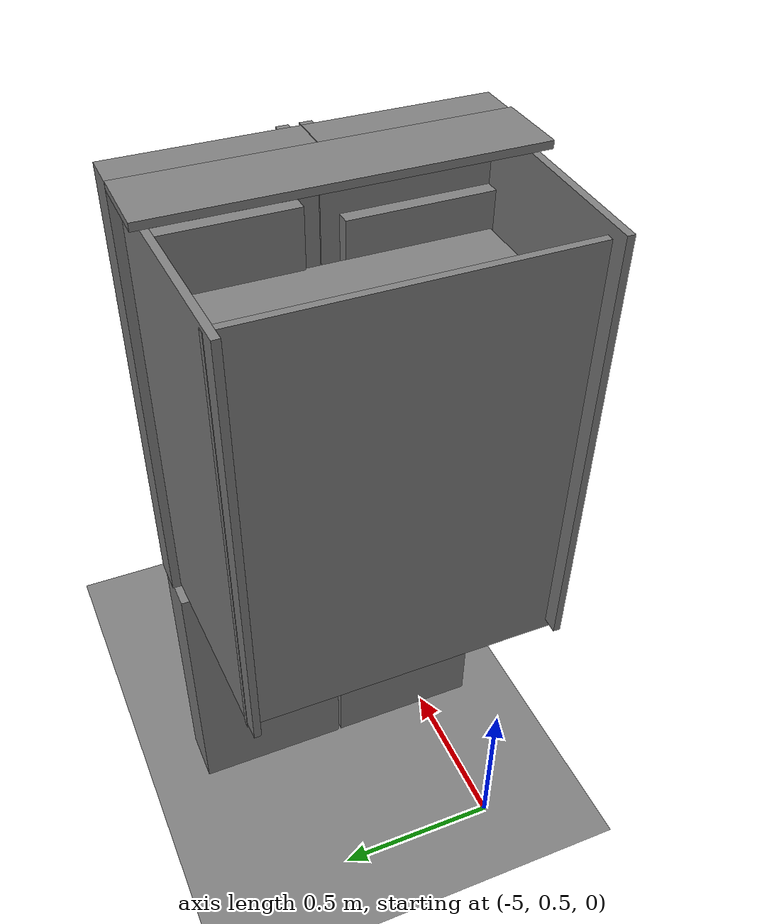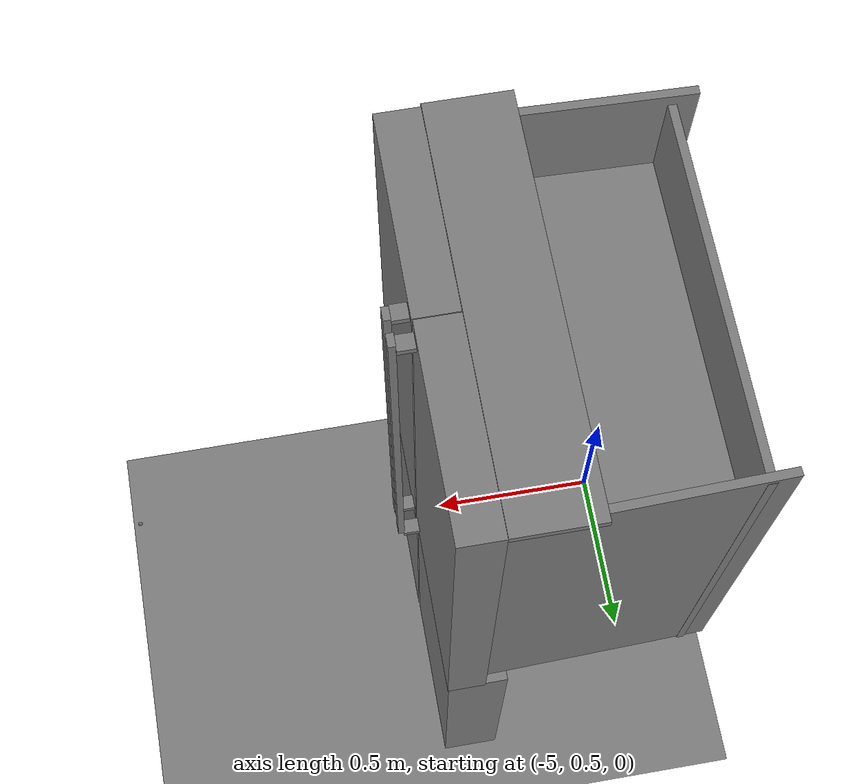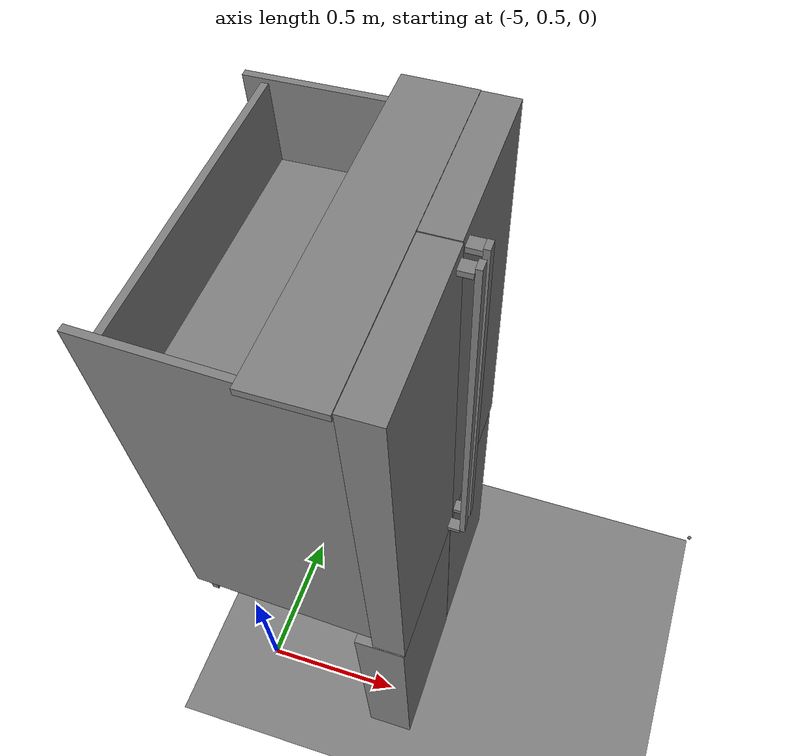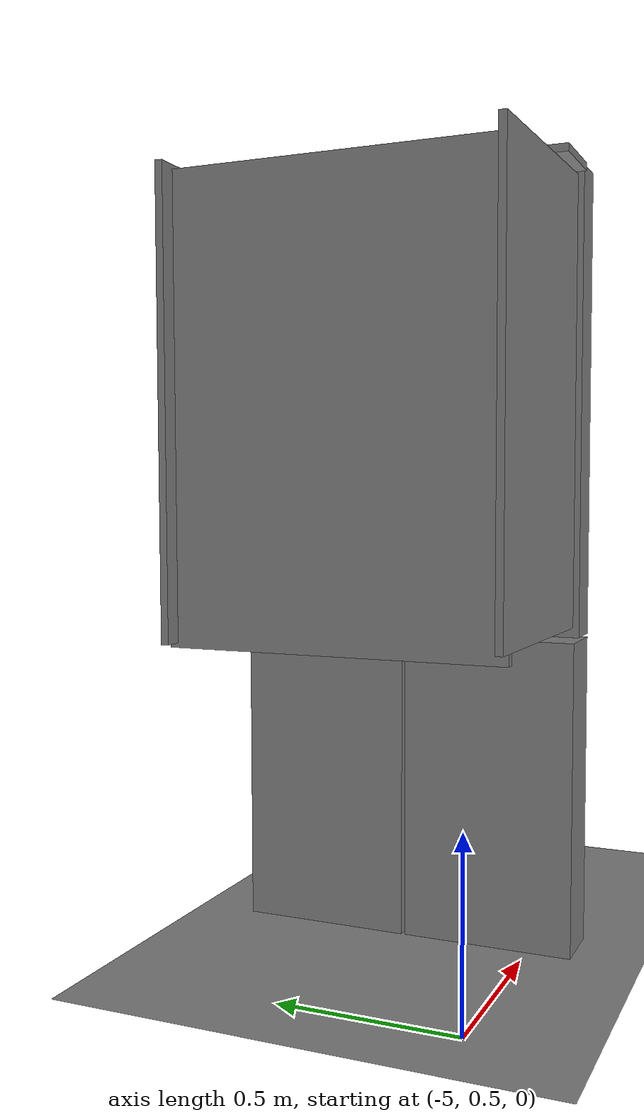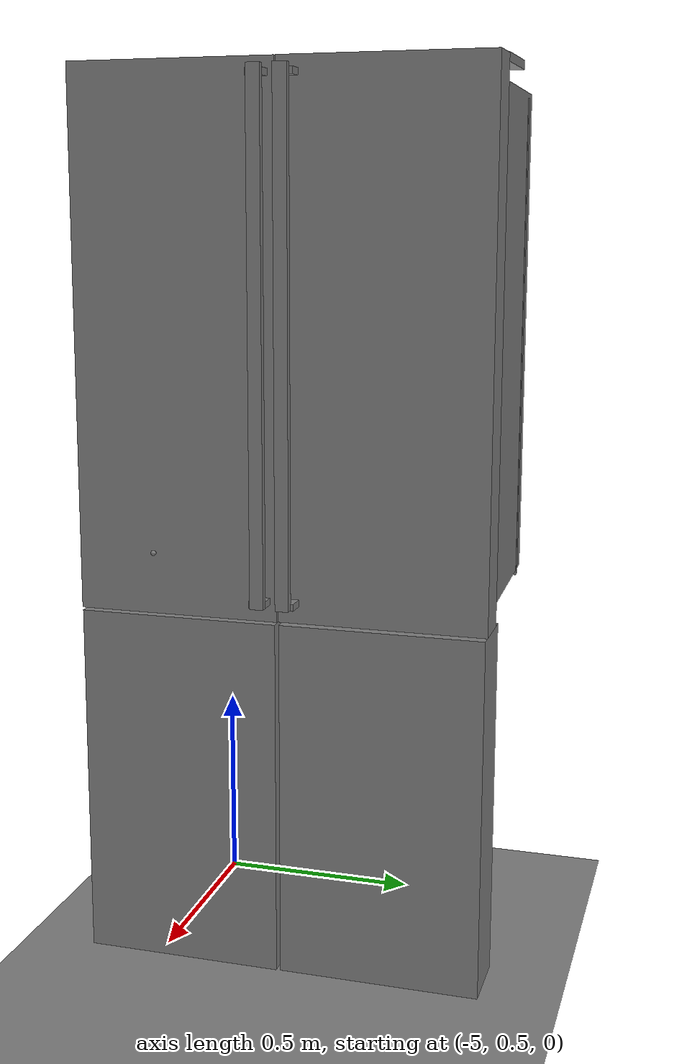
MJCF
<mujoco>
    <option gravity="0.000000000 0.000000000 -9.810000420" timestep="0.0049999999" integrator="implicitfast" density="1.225" viscosity="1.8000001e-05" noslip_iterations="10" iterations="100" sdf_iterations="50">
        <flag multiccd="disable"/>
    </option>
    <size memory="1000M"/>
    <compiler coordinate="local"/>
    <worldbody>
        <light cutoff="30" pos="0 1 1" dir="0 -1 -2"/>
        <light cutoff="30" pos="0 -1 1" dir="0 1 -2"/>
        <body pos="-4.455995083 0.348160446 1.533870339" euler="0.000000000 0.000000000 0.000000000" name="openloong_gripper_2f85_fix_base_usda_fridge_left_up">
            <geom contype="1" conaffinity="1" density="1000" type="box" material="" rgba="0.500000000 0.500000000 0.500000000 1.000000000" solimp="0.899999976 0.949999988 0.001000000" friction="1.000000000 0.005000000 0.000100000" solref="0.020000000 1.000000000" margin="0" condim="3" group="0" pos="0.034918308 0.246351242 -0.000000358" quat="1.000000000 0.000000000 0.000000000 0.000013381" size="0.052000001 0.243000001 0.625000000" name="openloong_gripper_2f85_fix_base_usda_Fridge_02_a_03993845_0EEC_4BC2_AA64_9A86490B8A33"/>
            <geom contype="1" conaffinity="1" density="1000" type="box" material="" rgba="0.500000000 0.500000000 0.500000000 1.000000000" solimp="0.899999976 0.949999988 0.001000000" friction="1.000000000 0.005000000 0.000100000" solref="0.020000000 1.000000000" margin="0" condim="3" group="0" pos="-0.055340290 0.240164995 -0.197626591" quat="0.999999940 0.000000000 0.000000000 0.000271916" size="0.035000000 0.200000003 0.075999998" name="openloong_gripper_2f85_fix_base_usda_Fridge_02_g_88184EF1_ADF1_48D8_94D8_8FDC906062DC"/>
            <geom contype="1" conaffinity="1" density="1000" type="box" material="" rgba="0.500000000 0.500000000 0.500000000 1.000000000" solimp="0.899999976 0.949999988 0.001000000" friction="1.000000000 0.005000000 0.000100000" solref="0.020000000 1.000000000" margin="0" condim="3" group="0" pos="-0.036716461 0.240169704 0.099823833" quat="1.000000000 0.000000000 0.000000000 0.000120342" size="0.020000000 0.200000003 0.070000000" name="openloong_gripper_2f85_fix_base_usda_Fridge_02_f_D22910BF_ACB7_42AA_9978_6A16A8F4C08B"/>
            <geom contype="1" conaffinity="1" density="1000" type="box" material="" rgba="0.500000000 0.500000000 0.500000000 1.000000000" solimp="0.899999976 0.949999988 0.001000000" friction="1.000000000 0.005000000 0.000100000" solref="0.020000000 1.000000000" margin="0" condim="3" group="0" pos="0.133846283 0.458910882 0.011316895" quat="1.000000000 0.000000000 0.000000000 0.000000417" size="0.008500000 0.016000001 0.595000029" name="openloong_gripper_2f85_fix_base_usda_Fridge_02_b_5BB47BA0_08E0_4889_AA0D_3F4C14DE0D3C"/>
            <geom contype="1" conaffinity="1" density="1000" type="box" material="" rgba="0.500000000 0.500000000 0.500000000 1.000000000" solimp="0.899999976 0.949999988 0.001000000" friction="1.000000000 0.005000000 0.000100000" solref="0.020000000 1.000000000" margin="0" condim="3" group="0" pos="-0.036197186 0.240169704 0.373237491" quat="1.000000000 0.000000000 0.000000000 0.000087470" size="0.020000000 0.200000003 0.070000000" name="openloong_gripper_2f85_fix_base_usda_Fridge_02_e_5FDBC4CB_BE53_4A77_8F01_1EFD7ECF49BF"/>
            <geom contype="1" conaffinity="1" density="1000" type="box" material="" rgba="0.500000000 0.500000000 0.500000000 1.000000000" solimp="0.899999976 0.949999988 0.001000000" friction="1.000000000 0.005000000 0.000100000" solref="0.020000000 1.000000000" margin="0" condim="3" group="0" pos="0.097751617 0.454878092 -0.576283276" quat="1.000000000 0.000000000 0.000000000 0.000000417" size="0.029999999 0.018999999 0.008000000" name="openloong_gripper_2f85_fix_base_usda_Fridge_02_c_51BCA0C8_B386_404D_A589_89DFC6CA8899"/>
            <geom contype="1" conaffinity="1" density="1000" type="box" material="" rgba="0.500000000 0.500000000 0.500000000 1.000000000" solimp="0.899999976 0.949999988 0.001000000" friction="1.000000000 0.005000000 0.000100000" solref="0.020000000 1.000000000" margin="0" condim="3" group="0" pos="0.096112251 0.454878092 0.589555621" quat="1.000000000 0.000000000 0.000000000 0.000000417" size="0.029999999 0.018999999 0.008000000" name="openloong_gripper_2f85_fix_base_usda_Fridge_02_d_D59DC015_A85C_47C6_B82D_9E5B979C0E75"/>
            <joint armature="0" stiffness="0" damping="5" axis="0.000000 0.000000 -1.000000" limited="true" range="0.000000000 180.000000000" type="hinge" name="openloong_gripper_2f85_fix_base_usda_fridge_left_up_joint"/>
        </body>
        <body pos="-4.456572533 1.328142047 1.533870339" euler="0.000000000 0.000000000 0.000000000" name="openloong_gripper_2f85_fix_base_usda_fridge_right_up">
            <geom contype="1" conaffinity="1" density="1000" type="box" material="" rgba="0.500000000 0.500000000 0.500000000 1.000000000" solimp="0.899999976 0.949999988 0.001000000" friction="1.000000000 0.005000000 0.000100000" solref="0.020000000 1.000000000" margin="0" condim="3" group="0" pos="-0.042358875 -0.244417667 0.003658533" quat="0.999999881 0.000000000 0.000000000 0.000160277" size="0.020000000 0.189999998 0.500000000" name="openloong_gripper_2f85_fix_base_usda_geom_96AB2A06_C2D1_47C8_85C6_294BE48DB823"/>
            <geom contype="1" conaffinity="1" density="1000" type="box" material="" rgba="0.500000000 0.500000000 0.500000000 1.000000000" solimp="0.899999976 0.949999988 0.001000000" friction="1.000000000 0.005000000 0.000100000" solref="0.020000000 1.000000000" margin="0" condim="3" group="0" pos="0.134432793 -0.461116314 0.011315942" quat="0.999999940 0.000000075 -0.000000089 0.000017196" size="0.008500000 0.016000001 0.595000029" name="openloong_gripper_2f85_fix_base_usda_geom_7F68B4D0_834E_41EE_806C_FDA729794AC5"/>
            <geom contype="1" conaffinity="1" density="1000" type="box" material="" rgba="0.500000000 0.500000000 0.500000000 1.000000000" solimp="0.899999976 0.949999988 0.001000000" friction="1.000000000 0.005000000 0.000100000" solref="0.020000000 1.000000000" margin="0" condim="3" group="0" pos="0.096698761 -0.456393361 0.589552999" quat="0.999999881 0.000000074 -0.000000089 0.000032246" size="0.029999999 0.018999999 0.008000000" name="openloong_gripper_2f85_fix_base_usda_geom_C39B69CD_3312_4BD8_85C3_A011180FB52A"/>
            <geom contype="1" conaffinity="1" density="1000" type="box" material="" rgba="0.500000000 0.500000000 0.500000000 1.000000000" solimp="0.899999976 0.949999988 0.001000000" friction="1.000000000 0.005000000 0.000100000" solref="0.020000000 1.000000000" margin="0" condim="3" group="0" pos="0.098338127 -0.456895828 -0.576284051" quat="0.999999940 0.000000074 -0.000000089 0.000029832" size="0.029999999 0.018999999 0.008000000" name="openloong_gripper_2f85_fix_base_usda_geom_93CD4DA1_736F_4105_A953_7F8CB7C0B18E"/>
            <geom contype="1" conaffinity="1" density="1000" type="box" material="" rgba="0.500000000 0.500000000 0.500000000 1.000000000" solimp="0.899999976 0.949999988 0.001000000" friction="1.000000000 0.005000000 0.000100000" solref="0.020000000 1.000000000" margin="0" condim="3" group="0" pos="0.034286022 -0.245587349 0.000602603" quat="0.999999881 0.000000000 0.000000000 0.000051796" size="0.050999999 0.243000001 0.625000000" name="openloong_gripper_2f85_fix_base_usda_geom_F97D5D1C_8A55_44AC_8615_676F327D7465"/>
            <joint armature="0" stiffness="0" damping="5" axis="0.000000 0.000000 1.000000" limited="true" range="0.000000000 180.000000000" type="hinge" name="openloong_gripper_2f85_fix_base_usda_fridge_right_up_joint"/>
        </body>
        <body pos="0.000000000 0.000000000 0.000000000" euler="0.000000000 0.000000000 0.000000000" name="StaticObjcets_StaticObjcets">
            <geom contype="2" conaffinity="2" density="1000" type="box" material="" rgba="0.500000000 0.500000000 0.500000000 1.000000000" solimp="0.899999976 0.949999988 0.001000000" friction="1.000000000 0.005000000 0.000100000" solref="0.020000000 1.000000000" margin="0" condim="3" group="0" pos="-4.761908531 0.835612714 1.871172667" quat="1.000000000 0.000000000 0.000000000 0.000000000" size="0.250000000 0.439999998 0.005000000" name="StaticObjcets_geom_A274048E_7CA4_4632_A5DB_0F850166AA10"/>
            <geom contype="2" conaffinity="2" density="1000" type="box" material="" rgba="0.500000000 0.500000000 0.500000000 1.000000000" solimp="0.899999976 0.949999988 0.001000000" friction="1.000000000 0.005000000 0.000100000" solref="0.020000000 1.000000000" margin="0" condim="3" group="0" pos="-4.769333839 0.386707336 1.535037637" quat="0.707029462 0.707027197 -0.010532650 -0.010532619" size="0.300000012 0.600000024 0.010000000" name="StaticObjcets_geom_CCD59319_8B58_4ACF_A2E3_B1F33B3E663B"/>
            <geom contype="2" conaffinity="2" density="1000" type="box" material="" rgba="0.500000000 0.500000000 0.500000000 1.000000000" solimp="0.899999976 0.949999988 0.001000000" friction="1.000000000 0.005000000 0.000100000" solref="0.020000000 1.000000000" margin="0" condim="3" group="0" pos="-4.763467789 0.835180044 1.691508532" quat="1.000000000 0.000000000 0.000000000 0.000000000" size="0.250000000 0.439999998 0.005000000" name="StaticObjcets_geom_7ED862DB_A7A9_4EBD_8779_07FA236A4631"/>
            <geom contype="2" conaffinity="2" density="1000" type="box" material="" rgba="0.500000000 0.500000000 0.500000000 1.000000000" solimp="0.899999976 0.949999988 0.001000000" friction="1.000000000 0.005000000 0.000100000" solref="0.020000000 1.000000000" margin="0" condim="3" group="0" pos="-4.454798698 1.079833508 0.470532238" quat="0.707107067 0.000000000 0.000000000 0.707106471" size="0.239999995 0.079999998 0.430000007" name="StaticObjcets_Fridge_03_E250BB8A_235D_4043_BA52_99053CD35805"/>
            <geom contype="1" conaffinity="1" density="1000" type="plane" material="" rgba="0.500000000 0.500000000 0.500000000 1.000000000" solimp="0.899999976 0.949999988 0.001000000" friction="1.000000000 0.005000000 0.000100000" solref="0.020000000 1.000000000" margin="0" condim="3" group="0" pos="-0.043989260 0.222946882 0.032030921" quat="1.000000000 0.000000000 0.000000000 0.000000000" size="8.000000000 8.000000000 1.000000000" name="StaticObjcets_geom_DF0547C8_1A42_4C5B_81C7_4522FB522D68"/>
            <geom contype="2" conaffinity="2" density="1000" type="box" material="" rgba="0.500000000 0.500000000 0.500000000 1.000000000" solimp="0.899999976 0.949999988 0.001000000" friction="1.000000000 0.005000000 0.000100000" solref="0.020000000 1.000000000" margin="0" condim="3" group="0" pos="-4.771282196 1.281533480 1.516736507" quat="0.707029462 0.707027197 0.010532652 0.010532617" size="0.300000012 0.600000024 0.010000000" name="StaticObjcets_geom_E9FB4633_7B52_414F_84D2_2A268A2B7107"/>
            <geom contype="2" conaffinity="2" density="1000" type="box" material="" rgba="0.500000000 0.500000000 0.500000000 1.000000000" solimp="0.899999976 0.949999988 0.001000000" friction="1.000000000 0.005000000 0.000100000" solref="0.020000000 1.000000000" margin="0" condim="3" group="0" pos="-4.765080929 0.836613894 1.500948071" quat="1.000000000 0.000000000 0.000000000 0.000000000" size="0.250000000 0.439999998 0.005000000" name="StaticObjcets_geom_33E8FA13_6394_45D1_A111_5BA9095C75EE"/>
            <geom contype="2" conaffinity="2" density="1000" type="box" material="" rgba="0.500000000 0.500000000 0.500000000 1.000000000" solimp="0.899999976 0.949999988 0.001000000" friction="1.000000000 0.005000000 0.000100000" solref="0.020000000 1.000000000" margin="0" condim="3" group="0" pos="-4.717486858 0.835144579 1.096694350" quat="1.000000000 0.000000000 0.000000000 0.000000000" size="0.200000003 0.439999998 0.119999997" name="StaticObjcets_geom_457E2138_7795_4D47_987E_AC362ECEA79E"/>
            <geom contype="2" conaffinity="2" density="1000" type="box" material="" rgba="0.500000000 0.500000000 0.500000000 1.000000000" solimp="0.899999976 0.949999988 0.001000000" friction="1.000000000 0.005000000 0.000100000" solref="0.020000000 1.000000000" margin="0" condim="3" group="0" pos="-4.453287601 0.590693057 0.470532209" quat="0.707107067 0.000000000 0.000000000 0.707106471" size="0.239999995 0.079999998 0.430000007" name="StaticObjcets_Fridge_04_a_2988A76A_99B7_41FC_BE5D_76BE2F8F2301"/>
            <geom contype="1" conaffinity="1" density="1000" type="box" material="" rgba="0.500000000 0.500000000 0.500000000 1.000000000" solimp="0.899999976 0.949999988 0.001000000" friction="1.000000000 0.005000000 0.000100000" solref="0.020000000 1.000000000" margin="0" condim="3" group="0" pos="-4.573544502 0.835462213 2.151423454" quat="1.000000000 0.000000000 0.000000000 0.000000000" size="0.100000001 0.490000010 0.010000000" name="StaticObjcets_geom_C2A4FF7B_9183_4EDA_9A4E_B0DB613D702C"/>
            <geom contype="2" conaffinity="2" density="1000" type="box" material="" rgba="0.500000000 0.500000000 0.500000000 1.000000000" solimp="0.899999976 0.949999988 0.001000000" friction="1.000000000 0.005000000 0.000100000" solref="0.020000000 1.000000000" margin="0" condim="3" group="0" pos="-5.012205601 0.835292637 1.504703879" quat="0.500000417 0.499999970 0.499999970 0.499999553" size="0.449999988 0.600000024 0.010000000" name="StaticObjcets_Fridge_only_08_1C380841_CDC2_4987_88C1_FCFD1A8A7FE6"/>
        </body>
        <body pos="-3.856808662 0.696573794 2.385196209" euler="111.454360962 85.381576538 57.998157501" mocap="true" name="spotlight3_SpotLight"/>
        <body pos="-3.734010696 1.052055597 2.386027336" euler="-4.347277641 54.031719208 60.424964905" mocap="true" name="spotlight1_SpotLight"/>
        <body pos="-3.601272583 0.855086744 2.379660130" euler="-96.132011414 -48.099407196 167.049530029" mocap="true" name="spotlight4_SpotLight"/>
        <body pos="-3.662749529 0.835145235 0.026324987" euler="0.000000000 0.000000000 180.000000000" mocap="true" name="openloong_gripper_2f85_fix_base_usda_leftHandMocap"/>
        <body pos="-3.662749529 0.835145235 0.026324987" euler="0.000000000 0.000000000 180.000000000" mocap="true" name="openloong_gripper_2f85_fix_base_usda_rightHandMocap"/>
        <body pos="-3.662749529 0.835145235 1.226325035" euler="0.000000000 0.000000000 180.000000000" name="openloong_gripper_2f85_fix_base_usda_base_link">
            <geom contype="1" conaffinity="1" density="1000" type="mesh" material="" rgba="0.783999979 0.783999979 0.783999979 1.000000000" solimp="0.899999976 0.949999988 0.001000000" friction="1.000000000 0.005000000 0.000100000" solref="0.020000000 1.000000000" margin="0" condim="3" group="3" mesh="base_link" pos="0.000000000 0.000000000 0.000000000" quat="1.000000000 0.000000000 0.000000000 0.000000000" size="1.000000000 1.000000000 1.000000000" name="openloong_gripper_2f85_fix_base_usda__geom_7_199BDED2_D772_459A_92F0_959967FC4A2E"/>
            <site size="0.005000000 0.005000000 0.005000000" rgba="0.500000000 0.500000000 0.500000000 1.000000000" pos="0.000000000 0.000000000 0.000000000" quat="1.000000000 0.000000000 0.000000000 0.000000000" group="0" type="sphere" name="openloong_gripper_2f85_fix_base_usda_imu"/>
            <inertial mass="22.447001" pos="-0.005664100 -0.001336700 0.238289997" diaginertia="0.374352545 0.277180195 0.220617250" quat="0.999247074 0.035235517 -0.015086859 0.006023135"/>
            <body pos="0.000000000 0.000000000 0.299999952" euler="0.000000000 0.000000000 0.000000000" name="openloong_gripper_2f85_fix_base_usda_dummy_body">
                <geom contype="1" conaffinity="1" density="1000" type="sphere" material="" rgba="0.783999979 0.783999979 0.783999979 1.000000000" solimp="0.899999976 0.949999988 0.001000000" friction="1.000000000 0.005000000 0.000100000" solref="0.020000000 1.000000000" margin="0" condim="3" group="3" pos="0.000000000 0.000000000 0.000000000" quat="1.000000000 0.000000000 0.000000000 0.000000000" size="0.010000000 0.000000000 0.000000000" name="openloong_gripper_2f85_fix_base_usda__geom_8_84056C3F_E5E6_4D80_9C78_7F381EF2FD91"/>
                <joint armature="0.0099999998" stiffness="0" damping="0.1" axis="0.000000 0.000000 1.000000" type="hinge" name="openloong_gripper_2f85_fix_base_usda_dummy_joint"/>
                <site size="0.010000000 0.005000000 0.005000000" rgba="0.500000000 0.500000000 0.500000000 1.000000000" pos="0.000000000 0.000000000 0.000000000" quat="1.000000000 0.000000000 0.000000000 0.000000000" group="3" type="sphere" name="openloong_gripper_2f85_fix_base_usda_dummy_site"/>
            </body>
            <body pos="0.009000063 0.000000000 0.406399965" euler="0.000000000 0.000000000 0.000000000" name="openloong_gripper_2f85_fix_base_usda_Link_head_yaw">
                <geom contype="1" conaffinity="1" density="1000" type="mesh" material="" rgba="0.783999979 0.783999979 0.783999979 1.000000000" solimp="0.899999976 0.949999988 0.001000000" friction="1.000000000 0.005000000 0.000100000" solref="0.020000000 1.000000000" margin="0" condim="3" group="3" mesh="Link_head_yaw" pos="0.000000000 0.000000000 0.000000000" quat="1.000000000 0.000000000 0.000000000 0.000000000" size="1.000000000 1.000000000 1.000000000" name="openloong_gripper_2f85_fix_base_usda__geom_10_40B7E01F_172E_48AD_8065_325AB79ABACB"/>
                <inertial mass="0.84249002" pos="0.000000000 -0.002081400 0.044801001" diaginertia="0.000700588 0.000629000 0.000553812" quat="0.706933022 -0.015675601 0.015677100 0.706933022"/>
                <body pos="0.000000000 -0.034600019 0.048500061" euler="0.000000000 0.000000000 0.000000000" name="openloong_gripper_2f85_fix_base_usda_Link_head_pitch">
                    <geom contype="1" conaffinity="1" density="1000" type="mesh" material="" rgba="0.783999979 0.783999979 0.783999979 1.000000000" solimp="0.899999976 0.949999988 0.001000000" friction="1.000000000 0.005000000 0.000100000" solref="0.020000000 1.000000000" margin="0" condim="3" group="3" mesh="Link_head_pitch" pos="0.000000000 0.000000000 0.000000000" quat="1.000000000 0.000000000 0.000000000 0.000000000" size="1.000000000 1.000000000 1.000000000" name="openloong_gripper_2f85_fix_base_usda__geom_12_36806FAD_E044_4E9C_8E36_8FCA33DF0095"/>
                    <inertial mass="1.3943" pos="0.020569000 0.033004001 0.125000000" diaginertia="0.006381400 0.006289940 0.004481460" quat="0.973390222 0.008406822 0.228157058 0.019624906"/>
                    <body pos="0.000000000 0.029999971 0.000000000" euler="0.000000000 0.000000000 0.000000000" name="openloong_gripper_2f85_fix_base_usda_neck_center_body">
                        <site size="0.010000000 0.005000000 0.005000000" rgba="0.500000000 0.500000000 0.500000000 1.000000000" pos="0.000000000 0.000000000 0.000000000" quat="1.000000000 0.000000000 0.000000000 0.000000000" group="3" type="sphere" name="openloong_gripper_2f85_fix_base_usda_neck_center_site"/>
                        <body pos="0.019999981 0.000000000 0.149999976" euler="-0.000002229 39.998176575 -90.000205994" name="openloong_gripper_2f85_fix_base_usda_camera_head">
                            <site size="0.010000000 0.005000000 0.005000000" rgba="0.500000000 0.500000000 0.500000000 1.000000000" pos="0.000000000 0.000000000 0.000000000" quat="1.000000000 0.000000000 0.000000000 0.000000000" group="3" type="sphere" name="openloong_gripper_2f85_fix_base_usda_camera_head_site"/>
                        </body>
                    </body>
                </body>
            </body>
            <body pos="0.003999949 -0.161599994 0.392199993" euler="0.000000000 0.000000000 0.000000000" name="openloong_gripper_2f85_fix_base_usda_Link_arm_r_01">
                <geom contype="1" conaffinity="1" density="1000" type="mesh" material="" rgba="0.783999979 0.783999979 0.783999979 1.000000000" solimp="0.899999976 0.949999988 0.001000000" friction="1.000000000 0.005000000 0.000100000" solref="0.020000000 1.000000000" margin="0" condim="3" group="3" mesh="Link_arm_r_01" pos="0.000000000 0.000000000 0.000000000" quat="1.000000000 0.000000000 0.000000000 0.000000000" size="1.000000000 1.000000000 1.000000000" name="openloong_gripper_2f85_fix_base_usda__geom_14_ACDDEDD9_3598_4E6D_ABBE_75A388AA39ED"/>
                <joint armature="0.0099999998" stiffness="0" damping="1" axis="0.000000 -1.000000 0.000000" limited="true" range="-170.000015259 170.000015259" type="hinge" name="openloong_gripper_2f85_fix_base_usda_J_arm_r_01"/>
                <inertial mass="0.75641" pos="0.004494600 -0.038293999 -0.000001874" diaginertia="0.000842990 0.000803050 0.000587120" quat="-0.000163502 0.707098067 0.000812463 0.707115054"/>
                <body pos="-0.042000055 -0.041000009 0.000000000" euler="0.000000000 0.000000000 0.000000000" name="openloong_gripper_2f85_fix_base_usda_Link_arm_r_02">
                    <geom contype="1" conaffinity="1" density="1000" type="mesh" material="" rgba="0.783999979 0.783999979 0.783999979 1.000000000" solimp="0.899999976 0.949999988 0.001000000" friction="1.000000000 0.005000000 0.000100000" solref="0.020000000 1.000000000" margin="0" condim="3" group="3" mesh="Link_arm_r_02" pos="0.000000000 0.000000000 0.000000000" quat="1.000000000 0.000000000 0.000000000 0.000000000" size="1.000000000 1.000000000 1.000000000" name="openloong_gripper_2f85_fix_base_usda__geom_16_D9018F0A_887D_4799_B68B_6DCE6B10CF08"/>
                    <joint armature="0.0099999998" stiffness="0" damping="1" axis="-1.000000 0.000000 0.000000" limited="true" range="-105.000244141 105.000244141" type="hinge" name="openloong_gripper_2f85_fix_base_usda_J_arm_r_02"/>
                    <inertial mass="0.98500001" pos="0.041999999 -0.067430697 0.000000000" diaginertia="0.002262690 0.001730990 0.001154020" quat="0.500000000 0.500000000 -0.500000000 0.500000000"/>
                    <body pos="0.042000055 -0.122599959 0.000000000" euler="0.000000000 0.000000000 0.000000000" name="openloong_gripper_2f85_fix_base_usda_Link_arm_r_03">
                        <geom contype="1" conaffinity="1" density="1000" type="mesh" material="" rgba="0.783999979 0.783999979 0.783999979 1.000000000" solimp="0.899999976 0.949999988 0.001000000" friction="1.000000000 0.005000000 0.000100000" solref="0.020000000 1.000000000" margin="0" condim="3" group="3" mesh="Link_arm_r_03" pos="0.000000000 0.000000000 0.000000000" quat="1.000000000 0.000000000 0.000000000 0.000000000" size="1.000000000 1.000000000 1.000000000" name="openloong_gripper_2f85_fix_base_usda__geom_18_BCFAF640_848B_4C30_A349_DC1087EF9ECF"/>
                        <joint armature="0.0099999998" stiffness="0" damping="1" axis="0.000000 -1.000000 0.000000" limited="true" range="-170.000015259 170.000015259" type="hinge" name="openloong_gripper_2f85_fix_base_usda_J_arm_r_03"/>
                        <inertial mass="0.95899999" pos="-0.001413580 -0.164663002 0.020757901" diaginertia="0.002101340 0.002064590 0.000754802" quat="0.560480952 0.454391927 -0.443732947 0.531497955"/>
                        <body pos="0.035300016 -0.177399993 0.024000049" euler="0.000000000 0.000000000 0.000000000" name="openloong_gripper_2f85_fix_base_usda_Link_arm_r_04">
                            <geom contype="1" conaffinity="1" density="1000" type="mesh" material="" rgba="0.783999979 0.783999979 0.783999979 1.000000000" solimp="0.899999976 0.949999988 0.001000000" friction="1.000000000 0.005000000 0.000100000" solref="0.020000000 1.000000000" margin="0" condim="3" group="3" mesh="Link_arm_r_04" pos="0.000000000 0.000000000 0.000000000" quat="1.000000000 0.000000000 0.000000000 0.000000000" size="1.000000000 1.000000000 1.000000000" name="openloong_gripper_2f85_fix_base_usda__geom_20_D0640962_49FB_4259_9B9B_BD564BEEA1C3"/>
                            <joint armature="0.0099999998" stiffness="0" damping="1" axis="-1.000000 0.000000 0.000000" limited="true" range="0.000000000 170.000015259" type="hinge" name="openloong_gripper_2f85_fix_base_usda_J_arm_r_04"/>
                            <inertial mass="0.60000002" pos="-0.038727000 -0.060766999 -0.021003000" diaginertia="0.001092610 0.000712422 0.000645102" quat="0.327701002 0.632602990 -0.467366993 0.523443997"/>
                            <body pos="-0.035300016 -0.103500009 -0.024000049" euler="0.000000000 0.000000000 0.000000000" name="openloong_gripper_2f85_fix_base_usda_Link_arm_r_05">
                                <geom contype="1" conaffinity="1" density="1000" type="mesh" material="" rgba="0.783999979 0.783999979 0.783999979 1.000000000" solimp="0.899999976 0.949999988 0.001000000" friction="1.000000000 0.005000000 0.000100000" solref="0.020000000 1.000000000" margin="0" condim="3" group="3" mesh="Link_arm_r_05" pos="0.000000000 0.000000000 0.000000000" quat="1.000000000 0.000000000 0.000000000 0.000000000" size="1.000000000 1.000000000 1.000000000" name="openloong_gripper_2f85_fix_base_usda__geom_22_BA086B42_466F_4380_A1DC_AF81C711084F"/>
                                <joint armature="0.0099999998" stiffness="0" damping="1" axis="0.000000 -1.000000 0.000000" limited="true" range="-170.000015259 170.000015259" type="hinge" name="openloong_gripper_2f85_fix_base_usda_J_arm_r_05"/>
                                <inertial mass="0.68976003" pos="0.000032712 -0.068658002 -0.000111780" diaginertia="0.002522510 0.002411100 0.000448695" quat="0.707660973 0.706543028 -0.002603360 0.002470550"/>
                                <body pos="-0.026499987 -0.196499944 0.000000000" euler="0.000000000 0.000000000 0.000000000" name="openloong_gripper_2f85_fix_base_usda_Link_arm_r_06">
                                    <geom contype="1" conaffinity="1" density="1000" type="mesh" material="" rgba="0.783999979 0.783999979 0.783999979 1.000000000" solimp="0.899999976 0.949999988 0.001000000" friction="1.000000000 0.005000000 0.000100000" solref="0.020000000 1.000000000" margin="0" condim="3" group="3" mesh="Link_arm_r_06" pos="0.000000000 0.000000000 0.000000000" quat="1.000000000 0.000000000 0.000000000 0.000000000" size="1.000000000 1.000000000 1.000000000" name="openloong_gripper_2f85_fix_base_usda__geom_24_B906ABCC_8535_4B33_AFBB_633582F51985"/>
                                    <joint armature="0.0099999998" stiffness="0" damping="1" axis="1.000000 0.000000 0.000000" limited="true" range="-105.000244141 105.000244141" type="hinge" name="openloong_gripper_2f85_fix_base_usda_J_arm_r_06"/>
                                    <inertial mass="0.28" pos="0.026078001 -0.000000896 0.001663700" diaginertia="0.000156930 0.000145601 0.000104979" quat="0.707080841 0.001851080 0.001883810 0.707127810"/>
                                    <body pos="0.026499987 0.000000000 0.031800032" euler="0.000000000 0.000000000 0.000000000" name="openloong_gripper_2f85_fix_base_usda_Link_arm_r_07">
                                        <geom contype="1" conaffinity="1" density="1000" type="mesh" material="" rgba="0.783999979 0.783999979 0.783999979 1.000000000" solimp="0.899999976 0.949999988 0.001000000" friction="1.000000000 0.005000000 0.000100000" solref="0.020000000 1.000000000" margin="0" condim="3" group="3" mesh="Link_arm_r_07" pos="0.000000000 0.000000000 0.000000000" quat="1.000000000 0.000000000 0.000000000 0.000000000" size="1.000000000 1.000000000 1.000000000" name="openloong_gripper_2f85_fix_base_usda__geom_26_AACB8F30_0420_4F96_A52F_B5DB339D7050"/>
                                        <joint armature="0.0099999998" stiffness="0" damping="1" axis="0.000000 0.000000 1.000000" limited="true" range="-60.000133514 60.000133514" type="hinge" name="openloong_gripper_2f85_fix_base_usda_J_arm_r_07"/>
                                        <inertial mass="0.61353999" pos="-0.007859000 -0.158170000 -0.027736001" diaginertia="0.003037610 0.002570910 0.000729379" quat="0.427542925 0.443532884 -0.553093910 0.560867906"/>
                                        <body pos="0.000000000 0.286999941 -0.269999981" euler="150.000350952 0.000000000 0.000000000" name="openloong_gripper_2f85_fix_base_usda_camera_wrist_r">
                                            <site size="0.010000000 0.005000000 0.005000000" rgba="0.500000000 0.500000000 0.500000000 1.000000000" pos="0.000000000 0.000000000 0.000000000" quat="1.000000000 0.000000000 0.000000000 0.000000000" group="3" type="sphere" name="openloong_gripper_2f85_fix_base_usda_camera_wrist_r_site"/>
                                        </body>
                                        <body pos="0.000000000 -0.220000029 -0.032999992" euler="0.000000000 0.000000000 179.999969482" name="openloong_gripper_2f85_fix_base_usda_ee_center_body_r">
                                            <site size="0.010000000 0.005000000 0.005000000" rgba="0.500000000 0.500000000 0.500000000 1.000000000" pos="0.000000000 0.000000000 0.000000000" quat="1.000000000 0.000000000 0.000000000 0.000000000" group="3" type="sphere" name="openloong_gripper_2f85_fix_base_usda_ee_center_site_r"/>
                                        </body>
                                        <body pos="0.000000000 -0.065999985 -0.031000018" euler="89.999984741 0.000000000 180.000000000" name="openloong_gripper_2f85_fix_base_usda_zbr_base_link">
                                            <geom contype="1" conaffinity="1" density="1000" type="mesh" material="" rgba="0.783999979 0.783999979 0.783999979 1.000000000" solimp="0.899999976 0.949999988 0.001000000" friction="1.000000000 0.005000000 0.000100000" solref="0.020000000 1.000000000" margin="0" condim="3" group="3" mesh="base" pos="0.000000000 0.000000000 0.000000000" quat="1.000000000 0.000000000 0.000000000 0.000000000" size="1.000000238 1.000000238 1.000000238" name="openloong_gripper_2f85_fix_base_usda__geom_30_CE7AB151_A5B7_4E28_9085_77BED67C89CF"/>
                                            <inertial mass="0.77744102" pos="0.000000000 -0.000027039 0.035467502" diaginertia="0.000260285 0.000225381 0.000152708" quat="0.999998808 -0.001528488 0.000000000 0.000000000"/>
                                            <body pos="-0.030601032 0.004750133 0.065704480" euler="-89.999977112 0.000000000 0.000000000" name="openloong_gripper_2f85_fix_base_usda_r_left_driver">
                                                <geom contype="1" conaffinity="1" density="1000" type="mesh" material="" rgba="0.783999979 0.783999979 0.783999979 1.000000000" solimp="0.899999976 0.949999988 0.001000000" friction="1.000000000 0.005000000 0.000100000" solref="0.020000000 1.000000000" margin="0" condim="3" group="3" mesh="driver" pos="0.030601032 0.054904357 -0.004699946" quat="0.707106709 0.707106590 0.000000000 0.000000000" size="1.000000238 1.000000238 1.000000238" name="openloong_gripper_2f85_fix_base_usda__geom_32_5F518B3E_C28C_4E82_91A1_63B4FCDC258E"/>
                                                <joint armature="0.0049999999" stiffness="0" damping="0.1" axis="0.000000 0.000000 1.000000" limited="true" range="0.000000000 51.566200256" type="hinge" name="openloong_gripper_2f85_fix_base_usda_r_left_driver_joint"/>
                                                <inertial mass="0.0089956298" pos="0.000000000 0.017754700 0.001073140" diaginertia="0.000001724 0.000001609 0.000000322" quat="0.681301236 0.732003212 0.000000000 0.000000000"/>
                                                <body pos="-0.031425007 0.004532219 -0.010200026" euler="0.000000000 0.000000000 180.000000000" name="openloong_gripper_2f85_fix_base_usda_r_left_coupler">
                                                    <geom contype="1" conaffinity="1" density="1000" type="mesh" material="" rgba="0.783999979 0.783999979 0.783999979 1.000000000" solimp="0.899999976 0.949999988 0.001000000" friction="1.000000000 0.005000000 0.000100000" solref="0.020000000 1.000000000" margin="0" condim="3" group="3" mesh="coupler" pos="-0.062026039 -0.050372254 0.005499960" quat="0.707106709 -0.707106590 0.000000000 0.000000000" size="1.000000238 1.000000238 1.000000238" name="openloong_gripper_2f85_fix_base_usda__geom_34_B55F65CC_A509_457A_BF06_93E260D1E5C3"/>
                                                    <inertial mass="0.0140974" pos="0.000000000 0.003012090 0.023217499" diaginertia="0.000004162 0.000003522 0.000000888" quat="0.705635548 -0.045590367 0.045590367 0.705635548"/>
                                                </body>
                                            </body>
                                            <body pos="-0.012700084 -0.011999848 0.072219983" euler="-89.999977112 0.000000000 0.000000000" name="openloong_gripper_2f85_fix_base_usda_r_left_spring_link">
                                                <geom contype="1" conaffinity="1" density="1000" type="mesh" material="" rgba="0.783999979 0.783999979 0.783999979 1.000000000" solimp="0.899999976 0.949999988 0.001000000" friction="1.000000000 0.005000000 0.000100000" solref="0.020000000 1.000000000" margin="0" condim="3" group="3" mesh="spring_link" pos="0.012700084 0.061419860 0.012050035" quat="0.707106709 0.707106590 0.000000000 0.000000000" size="1.000000238 1.000000238 1.000000238" name="openloong_gripper_2f85_fix_base_usda__geom_36_3C62D659_F780_4D74_BE84_E42FC2ACE88B"/>
                                                <joint armature="0.001" stiffness="0.050000001" damping="0.00125" axis="0.000000 0.000000 1.000000" limited="true" range="-17.000000000 51.566200256" type="hinge" name="openloong_gripper_2f85_fix_base_usda_r_left_spring_link_joint"/>
                                                <inertial mass="0.0221642" pos="-0.000000009 0.018162400 0.021265799" diaginertia="0.000008969 0.000006717 0.000002639" quat="0.663403213 -0.244737089 0.244737089 0.663403213"/>
                                                <body pos="-0.038208015 -0.042500269 0.002950073" euler="180.000000000 0.000000000 -0.002179886" name="openloong_gripper_2f85_fix_base_usda_r_left_follower">
                                                    <geom contype="1" conaffinity="1" density="1000" type="mesh" material="" rgba="0.783999979 0.783999979 0.783999979 1.000000000" solimp="0.899999976 0.949999988 0.001000000" friction="1.000000000 0.005000000 0.000100000" solref="0.020000000 1.000000000" margin="0" condim="3" group="3" mesh="follower" pos="0.050907861 -0.103919886 -0.009099962" quat="0.707106709 -0.707106590 0.000000000 -0.000000000" size="1.000000238 1.000000238 1.000000238" name="openloong_gripper_2f85_fix_base_usda__geom_39_165B9554_DA5B_48BD_8C6F_1D4EE7138B8F"/>
                                                    <geom contype="1" conaffinity="1" density="1000" type="mesh" material="" rgba="0.783999979 0.783999979 0.783999979 1.000000000" solimp="0.899999976 0.949999988 0.001000000" friction="1.000000000 0.005000000 0.000100000" solref="0.020000000 1.000000000" margin="0" condim="3" group="3" mesh="tongue" pos="0.050907861 -0.103919886 -0.009099962" quat="0.707106709 -0.707106590 0.000000000 -0.000000000" size="1.000000238 1.000000238 1.000000238" name="openloong_gripper_2f85_fix_base_usda__geom_40_F2BDA670_3D34_49FB_8C1D_E1170ED30283"/>
                                                    <joint armature="0.001" stiffness="0" damping="0.1" axis="0.000000 0.000000 1.000000" limited="true" range="-49.999961853 51.566200256" type="hinge" name="openloong_gripper_2f85_fix_base_usda_r_left_follower"/>
                                                    <inertial mass="0.0125222" pos="0.000000000 -0.011046000 0.012478600" diaginertia="0.000002674 0.000002456 0.000000602" quat="0.986436546 0.164143041 0.000000000 0.000000000"/>
                                                    <body pos="-0.037789829 -0.103916071 -0.009099962" euler="-89.999961853 0.000000000 -0.000000000" name="openloong_gripper_2f85_fix_base_usda_r_left_pad">
                                                        <geom contype="1" conaffinity="1" density="1000" type="box" material="" rgba="0.550000012 0.550000012 0.550000012 1.000000000" solimp="0.949999988 0.990000010 0.001000000" friction="0.699999988 0.005000000 0.000100000" solref="0.020000000 1.000000000" margin="0" condim="3" group="3" mass="1e-06" pos="0.043257486 -0.000000119 0.119999796" quat="0.999999821 0.000000000 0.000000000 0.000000000" size="0.002000001 0.011000003 0.009375002" name="openloong_gripper_2f85_fix_base_usda_r_left_pad1_41E92216_7C20_4450_9C04_9FB39E3E49E3"/>
                                                        <geom contype="1" conaffinity="1" density="1000" type="box" material="" rgba="0.449999988 0.449999988 0.449999988 1.000000000" solimp="0.949999988 0.990000010 0.001000000" friction="0.600000024 0.005000000 0.000100000" solref="0.020000000 1.000000000" margin="0" condim="3" group="3" mass="1e-06" pos="0.043257724 -0.000000119 0.138749987" quat="0.999999821 0.000000000 0.000000000 0.000000000" size="0.002000001 0.011000003 0.009375002" name="openloong_gripper_2f85_fix_base_usda_r_left_pad2_AF4348DE_68B8_4AF1_B009_413E06D9965F"/>
                                                    </body>
                                                </body>
                                            </body>
                                            <body pos="0.030601032 -0.004749895 0.065704480" euler="89.999984741 0.000000000 180.000000000" name="openloong_gripper_2f85_fix_base_usda_r_right_driver">
                                                <geom contype="1" conaffinity="1" density="1000" type="mesh" material="" rgba="0.783999979 0.783999979 0.783999979 1.000000000" solimp="0.899999976 0.949999988 0.001000000" friction="1.000000000 0.005000000 0.000100000" solref="0.020000000 1.000000000" margin="0" condim="3" group="3" mesh="driver" pos="0.030601032 0.054904357 -0.004699946" quat="0.707106829 0.707106709 0.000000000 0.000000000" size="1.000000238 1.000000238 1.000000238" name="openloong_gripper_2f85_fix_base_usda__geom_42_DBC480A6_FEDC_4CE5_8B18_D07F8798CA6F"/>
                                                <joint armature="0.0049999999" stiffness="0" damping="0.1" axis="0.000000 0.000000 1.000000" limited="true" range="0.000000000 51.566200256" type="hinge" name="openloong_gripper_2f85_fix_base_usda_r_right_driver_joint"/>
                                                <inertial mass="0.0089956298" pos="0.000000000 0.017754700 0.001073140" diaginertia="0.000001724 0.000001609 0.000000322" quat="0.681301236 0.732003212 0.000000000 0.000000000"/>
                                                <body pos="-0.031425007 0.004532219 -0.010200026" euler="0.000000000 0.000000000 180.000000000" name="openloong_gripper_2f85_fix_base_usda_r_right_coupler">
                                                    <geom contype="1" conaffinity="1" density="1000" type="mesh" material="" rgba="0.783999979 0.783999979 0.783999979 1.000000000" solimp="0.899999976 0.949999988 0.001000000" friction="1.000000000 0.005000000 0.000100000" solref="0.020000000 1.000000000" margin="0" condim="3" group="3" mesh="coupler" pos="-0.062026039 -0.050372254 0.005499960" quat="0.707106829 -0.707106709 0.000000000 0.000000000" size="1.000000238 1.000000238 1.000000238" name="openloong_gripper_2f85_fix_base_usda__geom_44_E2C290D2_044D_4D5A_84C9_2D8E7771E844"/>
                                                    <inertial mass="0.0140974" pos="0.000000000 0.003012090 0.023217499" diaginertia="0.000004162 0.000003522 0.000000888" quat="0.705635548 -0.045590367 0.045590367 0.705635548"/>
                                                </body>
                                            </body>
                                            <body pos="0.012700084 0.012000087 0.072219983" euler="89.999984741 0.000000000 180.000000000" name="openloong_gripper_2f85_fix_base_usda_r_right_spring_link">
                                                <geom contype="1" conaffinity="1" density="1000" type="mesh" material="" rgba="0.783999979 0.783999979 0.783999979 1.000000000" solimp="0.899999976 0.949999988 0.001000000" friction="1.000000000 0.005000000 0.000100000" solref="0.020000000 1.000000000" margin="0" condim="3" group="3" mesh="spring_link" pos="0.012700084 0.061419860 0.012050035" quat="0.707106829 0.707106709 0.000000000 0.000000000" size="1.000000238 1.000000238 1.000000238" name="openloong_gripper_2f85_fix_base_usda__geom_46_C2A0EA73_F341_4815_AE2F_CC0109634D53"/>
                                                <joint armature="0.001" stiffness="0.050000001" damping="0.00125" axis="0.000000 0.000000 1.000000" limited="true" range="-17.000000000 51.566200256" type="hinge" name="openloong_gripper_2f85_fix_base_usda_r_right_spring_link_joint"/>
                                                <inertial mass="0.0221642" pos="-0.000000009 0.018162400 0.021265799" diaginertia="0.000008969 0.000006717 0.000002639" quat="0.663403213 -0.244737089 0.244737089 0.663403213"/>
                                                <body pos="-0.038208015 -0.042500269 0.002949954" euler="180.000000000 0.000000000 0.000000000" name="openloong_gripper_2f85_fix_base_usda_r_right_follower">
                                                    <geom contype="1" conaffinity="1" density="1000" type="mesh" material="" rgba="0.783999979 0.783999979 0.783999979 1.000000000" solimp="0.899999976 0.949999988 0.001000000" friction="1.000000000 0.005000000 0.000100000" solref="0.020000000 1.000000000" margin="0" condim="3" group="3" mesh="tongue" pos="0.050907861 -0.103919886 -0.009099962" quat="0.707106829 -0.707106709 0.000000000 0.000000000" size="1.000000238 1.000000238 1.000000238" name="openloong_gripper_2f85_fix_base_usda__geom_49_D763B137_78B5_420D_8FBE_BF88396DC876"/>
                                                    <geom contype="1" conaffinity="1" density="1000" type="mesh" material="" rgba="0.783999979 0.783999979 0.783999979 1.000000000" solimp="0.899999976 0.949999988 0.001000000" friction="1.000000000 0.005000000 0.000100000" solref="0.020000000 1.000000000" margin="0" condim="3" group="3" mesh="follower" pos="0.050907861 -0.103919886 -0.009099962" quat="0.707106829 -0.707106709 0.000000000 0.000000000" size="1.000000238 1.000000238 1.000000238" name="openloong_gripper_2f85_fix_base_usda__geom_50_8A7772EB_B873_4526_82AD_66CC6E965D39"/>
                                                    <joint armature="0.001" stiffness="0" damping="0.1" axis="0.000000 0.000000 1.000000" limited="true" range="-49.999961853 51.566200256" type="hinge" name="openloong_gripper_2f85_fix_base_usda_r_right_follower_joint"/>
                                                    <inertial mass="0.0125222" pos="0.000000000 -0.011046000 0.012478600" diaginertia="0.000002674 0.000002456 0.000000602" quat="0.986436546 0.164143041 0.000000000 0.000000000"/>
                                                    <body pos="-0.037789829 -0.103915952 -0.009099962" euler="-89.999984741 0.000000000 0.000000000" name="openloong_gripper_2f85_fix_base_usda_r_right_pad">
                                                        <geom contype="1" conaffinity="1" density="1000" type="box" material="" rgba="0.550000012 0.550000012 0.550000012 1.000000000" solimp="0.949999988 0.990000010 0.001000000" friction="0.699999988 0.005000000 0.000100000" solref="0.020000000 1.000000000" margin="0" condim="3" group="3" mass="1e-06" pos="0.043257963 0.000000000 0.119999677" quat="1.000000000 0.000000000 0.000000000 0.000000000" size="0.002000001 0.011000003 0.009375002" name="openloong_gripper_2f85_fix_base_usda_r_right_pad1_CEBD0240_0487_4449_9C5B_E8F087648E5F"/>
                                                        <geom contype="1" conaffinity="1" density="1000" type="box" material="" rgba="0.449999988 0.449999988 0.449999988 1.000000000" solimp="0.949999988 0.990000010 0.001000000" friction="0.600000024 0.005000000 0.000100000" solref="0.020000000 1.000000000" margin="0" condim="3" group="3" mass="1e-06" pos="0.043257963 0.000000119 0.138750106" quat="1.000000000 0.000000000 0.000000000 0.000000000" size="0.002000001 0.011000003 0.009375002" name="openloong_gripper_2f85_fix_base_usda_r_right_pad2_F9B27E81_74B8_4078_9CA6_4F12879D176B"/>
                                                    </body>
                                                </body>
                                            </body>
                                        </body>
                                    </body>
                                </body>
                            </body>
                        </body>
                    </body>
                </body>
            </body>
            <body pos="0.003999949 0.161599994 0.392199993" euler="0.000000000 0.000000000 0.000000000" name="openloong_gripper_2f85_fix_base_usda_Link_arm_l_01">
                <geom contype="1" conaffinity="1" density="1000" type="mesh" material="" rgba="0.783999979 0.783999979 0.783999979 1.000000000" solimp="0.899999976 0.949999988 0.001000000" friction="1.000000000 0.005000000 0.000100000" solref="0.020000000 1.000000000" margin="0" condim="3" group="3" mesh="Link_arm_l_01" pos="0.000000000 0.000000000 0.000000000" quat="1.000000000 0.000000000 0.000000000 0.000000000" size="1.000000000 1.000000000 1.000000000" name="openloong_gripper_2f85_fix_base_usda__geom_52_3F442A28_2503_4D1A_B0BF_523D922A0A6C"/>
                <joint armature="0.0099999998" stiffness="0" damping="1" axis="0.000000 1.000000 0.000000" limited="true" range="-170.000015259 170.000015259" type="hinge" name="openloong_gripper_2f85_fix_base_usda_J_arm_l_01"/>
                <inertial mass="0.75640601" pos="-0.004494650 0.038294200 -0.000001874" diaginertia="0.000842986 0.000803053 0.000587115" quat="-0.000812496 0.707115054 0.000163424 0.707098067"/>
                <body pos="0.042000055 0.041000009 0.000000000" euler="0.000000000 0.000000000 0.000000000" name="openloong_gripper_2f85_fix_base_usda_Link_arm_l_02">
                    <geom contype="1" conaffinity="1" density="1000" type="mesh" material="" rgba="0.783999979 0.783999979 0.783999979 1.000000000" solimp="0.899999976 0.949999988 0.001000000" friction="1.000000000 0.005000000 0.000100000" solref="0.020000000 1.000000000" margin="0" condim="3" group="3" mesh="Link_arm_l_02" pos="0.000000000 0.000000000 0.000000000" quat="1.000000000 0.000000000 0.000000000 0.000000000" size="1.000000000 1.000000000 1.000000000" name="openloong_gripper_2f85_fix_base_usda__geom_54_012BC092_039B_4B1D_8A6C_0843DAB3044A"/>
                    <joint armature="0.0099999998" stiffness="0" damping="1" axis="-1.000000 0.000000 0.000000" limited="true" range="-105.000244141 105.000244141" type="hinge" name="openloong_gripper_2f85_fix_base_usda_J_arm_l_02"/>
                    <inertial mass="0.98500001" pos="-0.041999999 0.067430697 0.000000000" diaginertia="0.002262690 0.001730990 0.001154020" quat="0.500000000 0.500000000 -0.500000000 0.500000000"/>
                    <body pos="-0.042000055 0.122600019 0.000000000" euler="0.000000000 0.000000000 0.000000000" name="openloong_gripper_2f85_fix_base_usda_Link_arm_l_03">
                        <geom contype="1" conaffinity="1" density="1000" type="mesh" material="" rgba="0.783999979 0.783999979 0.783999979 1.000000000" solimp="0.899999976 0.949999988 0.001000000" friction="1.000000000 0.005000000 0.000100000" solref="0.020000000 1.000000000" margin="0" condim="3" group="3" mesh="Link_arm_l_03" pos="0.000000000 0.000000000 0.000000000" quat="1.000000000 0.000000000 0.000000000 0.000000000" size="1.000000000 1.000000000 1.000000000" name="openloong_gripper_2f85_fix_base_usda__geom_56_CA784CD2_B1EF_48CC_88DF_77C3E7C2DBC5"/>
                        <joint armature="0.0099999998" stiffness="0" damping="1" axis="0.000000 1.000000 0.000000" limited="true" range="-170.000015259 170.000015259" type="hinge" name="openloong_gripper_2f85_fix_base_usda_J_arm_l_03"/>
                        <inertial mass="0.95899999" pos="0.001413580 0.164663002 0.020757901" diaginertia="0.002101340 0.002064590 0.000754802" quat="0.443732947 0.531497955 -0.560480952 0.454391927"/>
                        <body pos="-0.035300016 0.177399993 0.024000049" euler="0.000000000 0.000000000 0.000000000" name="openloong_gripper_2f85_fix_base_usda_Link_arm_l_04">
                            <geom contype="1" conaffinity="1" density="1000" type="mesh" material="" rgba="0.783999979 0.783999979 0.783999979 1.000000000" solimp="0.899999976 0.949999988 0.001000000" friction="1.000000000 0.005000000 0.000100000" solref="0.020000000 1.000000000" margin="0" condim="3" group="3" mesh="Link_arm_l_04" pos="0.000000000 0.000000000 0.000000000" quat="1.000000000 0.000000000 0.000000000 0.000000000" size="1.000000000 1.000000000 1.000000000" name="openloong_gripper_2f85_fix_base_usda__geom_58_304B8D48_1FA6_4F1E_99A6_BC52B258AF46"/>
                            <joint armature="0.0099999998" stiffness="0" damping="1" axis="1.000000 0.000000 0.000000" limited="true" range="0.000000000 170.000015259" type="hinge" name="openloong_gripper_2f85_fix_base_usda_J_arm_l_04"/>
                            <inertial mass="0.60000002" pos="0.038727000 0.060767200 -0.021003200" diaginertia="0.001092570 0.000712419 0.000645098" quat="0.467370987 0.523440003 -0.327692002 0.632607996"/>
                            <body pos="0.035300016 0.103500009 -0.024000049" euler="0.000000000 0.000000000 0.000000000" name="openloong_gripper_2f85_fix_base_usda_Link_arm_l_05">
                                <geom contype="1" conaffinity="1" density="1000" type="mesh" material="" rgba="0.783999979 0.783999979 0.783999979 1.000000000" solimp="0.899999976 0.949999988 0.001000000" friction="1.000000000 0.005000000 0.000100000" solref="0.020000000 1.000000000" margin="0" condim="3" group="3" mesh="Link_arm_l_05" pos="0.000000000 0.000000000 0.000000000" quat="1.000000000 0.000000000 0.000000000 0.000000000" size="1.000000000 1.000000000 1.000000000" name="openloong_gripper_2f85_fix_base_usda__geom_60_A4713FA6_65C7_4118_9807_97F8D4B5FD27"/>
                                <joint armature="0.0099999998" stiffness="0" damping="1" axis="0.000000 1.000000 0.000000" limited="true" range="-170.000015259 170.000015259" type="hinge" name="openloong_gripper_2f85_fix_base_usda_J_arm_l_05"/>
                                <inertial mass="0.68976003" pos="-0.000032712 0.068658002 -0.000111780" diaginertia="0.002522510 0.002411100 0.000448695" quat="0.706543028 0.707660973 0.002470550 -0.002603360"/>
                                <body pos="0.026499987 0.196500003 0.000000000" euler="0.000000000 0.000000000 0.000000000" name="openloong_gripper_2f85_fix_base_usda_Link_arm_l_06">
                                    <geom contype="1" conaffinity="1" density="1000" type="mesh" material="" rgba="0.783999979 0.783999979 0.783999979 1.000000000" solimp="0.899999976 0.949999988 0.001000000" friction="1.000000000 0.005000000 0.000100000" solref="0.020000000 1.000000000" margin="0" condim="3" group="3" mesh="Link_arm_l_06" pos="0.000000000 0.000000000 0.000000000" quat="1.000000000 0.000000000 0.000000000 0.000000000" size="1.000000000 1.000000000 1.000000000" name="openloong_gripper_2f85_fix_base_usda__geom_62_9E42E269_78E1_4980_8AEF_E8F800894DF6"/>
                                    <joint armature="0.0099999998" stiffness="0" damping="1" axis="-1.000000 0.000000 0.000000" limited="true" range="-105.000244141 105.000244141" type="hinge" name="openloong_gripper_2f85_fix_base_usda_J_arm_l_06"/>
                                    <inertial mass="0.28" pos="-0.026077701 0.000000896 0.001663730" diaginertia="0.000156927 0.000145598 0.000104981" quat="0.707080841 -0.001851280 -0.001884020 0.707127810"/>
                                    <body pos="-0.026499987 0.000000000 0.031800032" euler="0.000000000 0.000000000 0.000000000" name="openloong_gripper_2f85_fix_base_usda_Link_arm_l_07">
                                        <geom contype="1" conaffinity="1" density="1000" type="mesh" material="" rgba="0.783999979 0.783999979 0.783999979 1.000000000" solimp="0.899999976 0.949999988 0.001000000" friction="1.000000000 0.005000000 0.000100000" solref="0.020000000 1.000000000" margin="0" condim="3" group="3" mesh="Link_arm_l_07" pos="0.000000000 0.000000000 0.000000000" quat="1.000000000 0.000000000 0.000000000 0.000000000" size="1.000000000 1.000000000 1.000000000" name="openloong_gripper_2f85_fix_base_usda__geom_64_29C36FD8_3C9B_4D56_8AD1_591BB193C496"/>
                                        <joint armature="0.0099999998" stiffness="0" damping="1" axis="0.000000 0.000000 1.000000" limited="true" range="-60.000133514 60.000133514" type="hinge" name="openloong_gripper_2f85_fix_base_usda_J_arm_l_07"/>
                                        <inertial mass="0.61353999" pos="-0.007787200 0.157049999 -0.027733000" diaginertia="0.003037200 0.002570420 0.000729374" quat="0.443562120 0.427539080 -0.560871124 0.553070128"/>
                                        <body pos="0.000000000 -0.287000000 -0.269999981" euler="-150.000350952 -0.000000001 179.976669312" name="openloong_gripper_2f85_fix_base_usda_camera_wrist_l">
                                            <site size="0.010000000 0.005000000 0.005000000" rgba="0.500000000 0.500000000 0.500000000 1.000000000" pos="0.000000000 0.000000000 0.000000000" quat="1.000000000 0.000000000 0.000000000 0.000000000" group="3" type="sphere" name="openloong_gripper_2f85_fix_base_usda_camera_wrist_l_site"/>
                                        </body>
                                        <body pos="0.000000000 0.219999999 -0.032999992" euler="0.000000000 0.000000000 0.000000000" name="openloong_gripper_2f85_fix_base_usda_ee_center_body">
                                            <site size="0.010000000 0.005000000 0.005000000" rgba="0.500000000 0.500000000 0.500000000 1.000000000" pos="0.000000000 0.000000000 0.000000000" quat="1.000000000 0.000000000 0.000000000 0.000000000" group="3" type="sphere" name="openloong_gripper_2f85_fix_base_usda_ee_center_site"/>
                                        </body>
                                        <body pos="0.000000000 0.066000000 -0.031000018" euler="-90.000007629 0.000000000 0.000000000" name="openloong_gripper_2f85_fix_base_usda_zbll_base_link">
                                            <geom contype="1" conaffinity="1" density="1000" type="mesh" material="" rgba="0.783999979 0.783999979 0.783999979 1.000000000" solimp="0.899999976 0.949999988 0.001000000" friction="1.000000000 0.005000000 0.000100000" solref="0.020000000 1.000000000" margin="0" condim="3" group="3" mesh="base" pos="0.000000000 0.000000000 0.000000000" quat="1.000000000 0.000000000 0.000000000 0.000000000" size="1.000000000 1.000000000 1.000000000" name="openloong_gripper_2f85_fix_base_usda__geom_68_66267CF2_66CC_4E63_83D3_809B9E71584F"/>
                                            <inertial mass="0.77744102" pos="0.000000000 -0.000027039 0.035467502" diaginertia="0.000260285 0.000225381 0.000152708" quat="0.999998808 -0.001528488 0.000000000 0.000000000"/>
                                            <body pos="-0.030601025 0.004750252 0.065704346" euler="-89.999992371 0.000000000 0.000000000" name="openloong_gripper_2f85_fix_base_usda_l_left_driver">
                                                <geom contype="1" conaffinity="1" density="1000" type="mesh" material="" rgba="0.783999979 0.783999979 0.783999979 1.000000000" solimp="0.899999976 0.949999988 0.001000000" friction="1.000000000 0.005000000 0.000100000" solref="0.020000000 1.000000000" margin="0" condim="3" group="3" mesh="driver" pos="0.030601025 0.054904491 -0.004699945" quat="0.707106829 0.707106709 0.000000000 0.000000000" size="1.000000000 1.000000000 1.000000000" name="openloong_gripper_2f85_fix_base_usda__geom_70_0E93D033_F7D1_48A0_AB9A_90C374BD6141"/>
                                                <joint armature="0.0049999999" stiffness="0" damping="0.1" axis="0.000000 0.000000 1.000000" limited="true" range="0.000000000 51.566200256" type="hinge" name="openloong_gripper_2f85_fix_base_usda_l_left_driver_joint"/>
                                                <inertial mass="0.0089956298" pos="0.000000000 0.017754700 0.001073140" diaginertia="0.000001724 0.000001609 0.000000322" quat="0.681301236 0.732003212 0.000000000 0.000000000"/>
                                                <body pos="-0.031424999 0.004532233 -0.010200024" euler="0.000000000 0.000000000 180.000000000" name="openloong_gripper_2f85_fix_base_usda_l_left_coupler">
                                                    <geom contype="1" conaffinity="1" density="1000" type="mesh" material="" rgba="0.783999979 0.783999979 0.783999979 1.000000000" solimp="0.899999976 0.949999988 0.001000000" friction="1.000000000 0.005000000 0.000100000" solref="0.020000000 1.000000000" margin="0" condim="3" group="3" mesh="coupler" pos="-0.062026024 -0.050372299 0.005499959" quat="0.707106829 -0.707106709 0.000000000 0.000000000" size="1.000000000 1.000000000 1.000000000" name="openloong_gripper_2f85_fix_base_usda__geom_72_C414B5AD_50E2_4D4E_AFAE_BAC3557E8837"/>
                                                    <inertial mass="0.0140974" pos="0.000000000 0.003012090 0.023217499" diaginertia="0.000004162 0.000003522 0.000000888" quat="0.705635548 -0.045590367 0.045590367 0.705635548"/>
                                                </body>
                                            </body>
                                            <body pos="-0.012700081 -0.011999846 0.072219968" euler="-89.999992371 0.000000000 0.000000000" name="openloong_gripper_2f85_fix_base_usda_l_left_spring_link">
                                                <geom contype="1" conaffinity="1" density="1000" type="mesh" material="" rgba="0.783999979 0.783999979 0.783999979 1.000000000" solimp="0.899999976 0.949999988 0.001000000" friction="1.000000000 0.005000000 0.000100000" solref="0.020000000 1.000000000" margin="0" condim="3" group="3" mesh="spring_link" pos="0.012700081 0.061420009 0.012050033" quat="0.707106829 0.707106709 0.000000000 0.000000000" size="1.000000000 1.000000000 1.000000000" name="openloong_gripper_2f85_fix_base_usda__geom_74_8B65A3C5_62E8_4F6E_BF12_D367E0E06030"/>
                                                <joint armature="0.001" stiffness="0.050000001" damping="0.00125" axis="0.000000 0.000000 1.000000" limited="true" range="-17.000000000 51.566200256" type="hinge" name="openloong_gripper_2f85_fix_base_usda_l_left_spring_link_joint"/>
                                                <inertial mass="0.0221642" pos="-0.000000009 0.018162400 0.021265799" diaginertia="0.000008969 0.000006717 0.000002639" quat="0.663403213 -0.244737089 0.244737089 0.663403213"/>
                                                <body pos="-0.038208008 -0.042500287 0.002949953" euler="180.000000000 0.000000000 -0.002179887" name="openloong_gripper_2f85_fix_base_usda_l_left_follower">
                                                    <geom contype="1" conaffinity="1" density="1000" type="mesh" material="" rgba="0.783999979 0.783999979 0.783999979 1.000000000" solimp="0.899999976 0.949999988 0.001000000" friction="1.000000000 0.005000000 0.000100000" solref="0.020000000 1.000000000" margin="0" condim="3" group="3" mesh="follower" pos="0.050908089 -0.103920005 -0.009099960" quat="0.707106829 -0.707106709 0.000000000 -0.000000000" size="1.000000000 1.000000000 1.000000000" name="openloong_gripper_2f85_fix_base_usda__geom_77_30B8CE5D_5726_4B31_94AE_16142EDE70F4"/>
                                                    <geom contype="1" conaffinity="1" density="1000" type="mesh" material="" rgba="0.783999979 0.783999979 0.783999979 1.000000000" solimp="0.899999976 0.949999988 0.001000000" friction="1.000000000 0.005000000 0.000100000" solref="0.020000000 1.000000000" margin="0" condim="3" group="3" mesh="tongue" pos="0.050908089 -0.103920005 -0.009099960" quat="0.707106829 -0.707106709 0.000000000 -0.000000000" size="1.000000000 1.000000000 1.000000000" name="openloong_gripper_2f85_fix_base_usda__geom_78_8C11D191_4A1A_4AB4_886E_4E9349763ED8"/>
                                                    <joint armature="0.001" stiffness="0" damping="0.1" axis="0.000000 0.000000 1.000000" limited="true" range="-49.999961853 51.566200256" type="hinge" name="openloong_gripper_2f85_fix_base_usda_l_left_follower"/>
                                                    <inertial mass="0.0125222" pos="0.000000000 -0.011046000 0.012478600" diaginertia="0.000002674 0.000002456 0.000000602" quat="0.986436546 0.164143041 0.000000000 0.000000000"/>
                                                    <body pos="-0.037789583 -0.103916004 -0.009099960" euler="-89.999984741 0.000000000 -0.000000000" name="openloong_gripper_2f85_fix_base_usda_l_left_pad">
                                                        <geom contype="1" conaffinity="1" density="1000" type="box" material="" rgba="0.449999988 0.449999988 0.449999988 1.000000000" solimp="0.949999988 0.990000010 0.001000000" friction="0.600000024 0.005000000 0.000100000" solref="0.020000000 1.000000000" margin="0" condim="3" group="3" mass="1e-06" pos="0.043257952 0.000000000 0.138750181" quat="1.000000000 0.000000000 0.000000000 0.000000000" size="0.002000000 0.011000000 0.009375000" name="openloong_gripper_2f85_fix_base_usda_l_left_pad2_DD09682F_B72E_40C3_9F98_F2216BCB2131"/>
                                                        <geom contype="1" conaffinity="1" density="1000" type="box" material="" rgba="0.550000012 0.550000012 0.550000012 1.000000000" solimp="0.949999988 0.990000010 0.001000000" friction="0.699999988 0.005000000 0.000100000" solref="0.020000000 1.000000000" margin="0" condim="3" group="3" mass="1e-06" pos="0.043257952 0.000000000 0.119999990" quat="1.000000000 0.000000000 0.000000000 0.000000000" size="0.002000000 0.011000000 0.009375000" name="openloong_gripper_2f85_fix_base_usda_l_left_pad1_37040D30_F4F8_4419_A30F_8855F8819B20"/>
                                                    </body>
                                                </body>
                                            </body>
                                            <body pos="0.030601025 -0.004749894 0.065704346" euler="89.999992371 0.000000000 180.000000000" name="openloong_gripper_2f85_fix_base_usda_l_right_driver">
                                                <geom contype="1" conaffinity="1" density="1000" type="mesh" material="" rgba="0.783999979 0.783999979 0.783999979 1.000000000" solimp="0.899999976 0.949999988 0.001000000" friction="1.000000000 0.005000000 0.000100000" solref="0.020000000 1.000000000" margin="0" condim="3" group="3" mesh="driver" pos="0.030601025 0.054904498 -0.004699945" quat="0.707106829 0.707106709 0.000000000 0.000000000" size="1.000000000 1.000000000 1.000000000" name="openloong_gripper_2f85_fix_base_usda__geom_80_BC1AECFD_9657_4D23_B2B9_B9A5993647A9"/>
                                                <joint armature="0.0049999999" stiffness="0" damping="0.1" axis="0.000000 0.000000 1.000000" limited="true" range="0.000000000 51.566200256" type="hinge" name="openloong_gripper_2f85_fix_base_usda_l_right_driver_joint"/>
                                                <inertial mass="0.0089956298" pos="0.000000000 0.017754700 0.001073140" diaginertia="0.000001724 0.000001609 0.000000322" quat="0.681301236 0.732003212 0.000000000 0.000000000"/>
                                                <body pos="-0.031424999 0.004532233 -0.010200024" euler="0.000000000 0.000000000 180.000000000" name="openloong_gripper_2f85_fix_base_usda_l_right_coupler">
                                                    <geom contype="1" conaffinity="1" density="1000" type="mesh" material="" rgba="0.783999979 0.783999979 0.783999979 1.000000000" solimp="0.899999976 0.949999988 0.001000000" friction="1.000000000 0.005000000 0.000100000" solref="0.020000000 1.000000000" margin="0" condim="3" group="3" mesh="coupler" pos="-0.062026024 -0.050372299 0.005499959" quat="0.707106829 -0.707106709 0.000000000 0.000000000" size="1.000000000 1.000000000 1.000000000" name="openloong_gripper_2f85_fix_base_usda__geom_82_A5F32F44_E585_4115_B29A_13EBAED02C94"/>
                                                    <inertial mass="0.0140974" pos="0.000000000 0.003012090 0.023217499" diaginertia="0.000004162 0.000003522 0.000000888" quat="0.705635548 -0.045590367 0.045590367 0.705635548"/>
                                                </body>
                                            </body>
                                            <body pos="0.012700081 0.012000084 0.072219968" euler="89.999992371 0.000000000 180.000000000" name="openloong_gripper_2f85_fix_base_usda_l_right_spring_link">
                                                <geom contype="1" conaffinity="1" density="1000" type="mesh" material="" rgba="0.783999979 0.783999979 0.783999979 1.000000000" solimp="0.899999976 0.949999988 0.001000000" friction="1.000000000 0.005000000 0.000100000" solref="0.020000000 1.000000000" margin="0" condim="3" group="3" mesh="spring_link" pos="0.012700081 0.061420005 0.012050033" quat="0.707106829 0.707106709 0.000000000 0.000000000" size="1.000000000 1.000000000 1.000000000" name="openloong_gripper_2f85_fix_base_usda__geom_84_62618528_CF02_4701_B4A1_AB47F603189C"/>
                                                <joint armature="0.001" stiffness="0.050000001" damping="0.00125" axis="0.000000 0.000000 1.000000" limited="true" range="-17.000000000 51.566200256" type="hinge" name="openloong_gripper_2f85_fix_base_usda_l_right_spring_link_joint"/>
                                                <inertial mass="0.0221642" pos="-0.000000009 0.018162400 0.021265799" diaginertia="0.000008969 0.000006717 0.000002639" quat="0.663403213 -0.244737089 0.244737089 0.663403213"/>
                                                <body pos="-0.038208008 -0.042500295 0.002949953" euler="180.000000000 0.000000000 0.000000000" name="openloong_gripper_2f85_fix_base_usda_l_right_follower">
                                                    <geom contype="1" conaffinity="1" density="1000" type="mesh" material="" rgba="0.783999979 0.783999979 0.783999979 1.000000000" solimp="0.899999976 0.949999988 0.001000000" friction="1.000000000 0.005000000 0.000100000" solref="0.020000000 1.000000000" margin="0" condim="3" group="3" mesh="tongue" pos="0.050907850 -0.103919998 -0.009100080" quat="0.707106829 -0.707106709 0.000000000 0.000000000" size="1.000000000 1.000000000 1.000000000" name="openloong_gripper_2f85_fix_base_usda__geom_87_8CCA49D1_8690_40FD_82DD_10C689EB6C28"/>
                                                    <geom contype="1" conaffinity="1" density="1000" type="mesh" material="" rgba="0.783999979 0.783999979 0.783999979 1.000000000" solimp="0.899999976 0.949999988 0.001000000" friction="1.000000000 0.005000000 0.000100000" solref="0.020000000 1.000000000" margin="0" condim="3" group="3" mesh="follower" pos="0.050907850 -0.103919998 -0.009100080" quat="0.707106829 -0.707106709 0.000000000 0.000000000" size="1.000000000 1.000000000 1.000000000" name="openloong_gripper_2f85_fix_base_usda__geom_88_FA34D8C2_54E0_4A4E_9B7D_386CB7F61907"/>
                                                    <joint armature="0.001" stiffness="0" damping="0.1" axis="0.000000 0.000000 1.000000" limited="true" range="-49.999961853 51.566200256" type="hinge" name="openloong_gripper_2f85_fix_base_usda_l_right_follower_joint"/>
                                                    <inertial mass="0.0125222" pos="0.000000000 -0.011046000 0.012478600" diaginertia="0.000002674 0.000002456 0.000000602" quat="0.986436546 0.164143041 0.000000000 0.000000000"/>
                                                    <body pos="-0.037789583 -0.103915997 -0.009100080" euler="-89.999984741 0.000000000 0.000000000" name="openloong_gripper_2f85_fix_base_usda_l_right_pad">
                                                        <geom contype="1" conaffinity="1" density="1000" type="box" material="" rgba="0.449999988 0.449999988 0.449999988 1.000000000" solimp="0.949999988 0.990000010 0.001000000" friction="0.600000024 0.005000000 0.000100000" solref="0.020000000 1.000000000" margin="0" condim="3" group="3" mass="1e-06" pos="0.043257952 0.000000119 0.138749987" quat="1.000000000 0.000000000 0.000000000 0.000000000" size="0.002000000 0.011000000 0.009375000" name="openloong_gripper_2f85_fix_base_usda_l_right_pad2_4D8D555D_8B5A_4113_A162_B86BDE6C86F2"/>
                                                        <geom contype="1" conaffinity="1" density="1000" type="box" material="" rgba="0.550000012 0.550000012 0.550000012 1.000000000" solimp="0.949999988 0.990000010 0.001000000" friction="0.699999988 0.005000000 0.000100000" solref="0.020000000 1.000000000" margin="0" condim="3" group="3" mass="1e-06" pos="0.043257952 0.000000000 0.119999975" quat="1.000000000 0.000000000 0.000000000 0.000000000" size="0.002000000 0.011000000 0.009375000" name="openloong_gripper_2f85_fix_base_usda_l_right_pad1_140FDB2E_75EE_4A63_A698_1D2E1723DC6F"/>
                                                    </body>
                                                </body>
                                            </body>
                                        </body>
                                    </body>
                                </body>
                            </body>
                        </body>
                    </body>
                </body>
            </body>
            <body pos="0.000000000 -0.065249979 0.000000000" euler="0.000000000 0.000000000 0.000000000" name="openloong_gripper_2f85_fix_base_usda_Link_waist_pitch">
                <geom contype="1" conaffinity="1" density="1000" type="mesh" material="" rgba="0.783999979 0.783999979 0.783999979 1.000000000" solimp="0.899999976 0.949999988 0.001000000" friction="1.000000000 0.005000000 0.000100000" solref="0.020000000 1.000000000" margin="0" condim="3" group="3" mesh="Link_waist_pitch" pos="0.000000000 0.000000000 0.000000000" quat="1.000000000 0.000000000 0.000000000 0.000000000" size="1.000000000 1.000000000 1.000000000" name="openloong_gripper_2f85_fix_base_usda__geom_90_09CDD473_9F19_44AF_981A_A906F68E7D4F"/>
                <inertial mass="2.6963999" pos="-0.000734960 0.049924999 -0.000029695" diaginertia="0.006190620 0.005201250 0.004737120" quat="0.524125040 0.474713057 -0.522095084 0.476820052"/>
                <body pos="-0.063999891 0.065500021 0.000000000" euler="0.000000000 0.000000000 0.000000000" name="openloong_gripper_2f85_fix_base_usda_Link_waist_roll">
                    <geom contype="1" conaffinity="1" density="1000" type="mesh" material="" rgba="0.783999979 0.783999979 0.783999979 1.000000000" solimp="0.899999976 0.949999988 0.001000000" friction="1.000000000 0.005000000 0.000100000" solref="0.020000000 1.000000000" margin="0" condim="3" group="3" mesh="Link_waist_roll" pos="0.000000000 0.000000000 0.000000000" quat="1.000000000 0.000000000 0.000000000 0.000000000" size="1.000000000 1.000000000 1.000000000" name="openloong_gripper_2f85_fix_base_usda__geom_92_04D7E566_3C50_45B4_8497_934A5F00AF75"/>
                    <inertial mass="2.9806001" pos="-0.003742400 -0.001000000 -0.016856000" diaginertia="0.018825000 0.017314700 0.005873970" quat="0.576995134 0.408750087 0.408750087 0.576995134"/>
                    <body pos="0.067500114 0.000000000 -0.098000050" euler="0.000000000 0.000000000 0.000000000" name="openloong_gripper_2f85_fix_base_usda_Link_waist_yaw">
                        <geom contype="1" conaffinity="1" density="1000" type="mesh" material="" rgba="0.783999979 0.783999979 0.783999979 1.000000000" solimp="0.899999976 0.949999988 0.001000000" friction="1.000000000 0.005000000 0.000100000" solref="0.020000000 1.000000000" margin="0" condim="3" group="3" mesh="Link_waist_yaw" pos="0.000000000 0.000000000 0.000000000" quat="1.000000000 0.000000000 0.000000000 0.000000000" size="1.000000000 1.000000000 1.000000000" name="openloong_gripper_2f85_fix_base_usda__geom_94_68D7D626_4C61_40D0_AEEE_5F568D407273"/>
                        <inertial mass="7.3587999" pos="-0.096171997 -0.001000000 -0.057836000" diaginertia="0.109522998 0.089752100 0.032765999" quat="0.571972013 0.571972013 -0.415749997 0.415749997"/>
                        <body pos="-0.087500095 -0.120000005 -0.069000006" euler="0.000000000 0.000000000 0.000000000" name="openloong_gripper_2f85_fix_base_usda_Link_hip_r_roll">
                            <geom contype="1" conaffinity="1" density="1000" type="mesh" material="" rgba="0.783999979 0.783999979 0.783999979 1.000000000" solimp="0.899999976 0.949999988 0.001000000" friction="1.000000000 0.005000000 0.000100000" solref="0.020000000 1.000000000" margin="0" condim="3" group="3" mesh="Link_hip_r_roll" pos="0.000000000 0.000000000 0.000000000" quat="1.000000000 0.000000000 0.000000000 0.000000000" size="1.000000000 1.000000000 1.000000000" name="openloong_gripper_2f85_fix_base_usda__geom_96_10D94266_E016_46AF_A551_085166DDCE9E"/>
                            <inertial mass="2.4333999" pos="0.075724997 -0.001061600 0.016590999" diaginertia="0.004506770 0.003996270 0.003606060" quat="0.357336968 0.610613942 0.606069922 0.363510966"/>
                            <body pos="0.082250118 -0.000999987 -0.009999990" euler="0.000000000 0.000000000 0.000000000" name="openloong_gripper_2f85_fix_base_usda_Link_hip_r_yaw">
                                <geom contype="1" conaffinity="1" density="1000" type="mesh" material="" rgba="0.783999979 0.783999979 0.783999979 1.000000000" solimp="0.899999976 0.949999988 0.001000000" friction="1.000000000 0.005000000 0.000100000" solref="0.020000000 1.000000000" margin="0" condim="3" group="3" mesh="Link_hip_r_yaw" pos="0.000000000 0.000000000 0.000000000" quat="1.000000000 0.000000000 0.000000000 0.000000000" size="1.000000000 1.000000000 1.000000000" name="openloong_gripper_2f85_fix_base_usda__geom_98_B06B68AA_C13F_4E59_BB7F_730C6795413C"/>
                                <inertial mass="3.4303" pos="-0.000000031 -0.007135600 -0.100630000" diaginertia="0.008090100 0.007736500 0.006631600" quat="0.706536055 0.028403703 -0.028403703 0.706536055"/>
                                <body pos="0.000000000 0.036750019 -0.105499983" euler="0.000000000 0.000000000 0.000000000" name="openloong_gripper_2f85_fix_base_usda_Link_hip_r_pitch">
                                    <geom contype="1" conaffinity="1" density="1000" type="mesh" material="" rgba="0.783999979 0.783999979 0.783999979 1.000000000" solimp="0.899999976 0.949999988 0.001000000" friction="1.000000000 0.005000000 0.000100000" solref="0.020000000 1.000000000" margin="0" condim="3" group="3" mesh="Link_hip_r_pitch" pos="0.000000000 0.000000000 0.000000000" quat="1.000000000 0.000000000 0.000000000 0.000000000" size="1.000000000 1.000000000 1.000000000" name="openloong_gripper_2f85_fix_base_usda__geom_100_CEB3045B_C8BF_41C8_9BC2_995A15BE1CC2"/>
                                    <inertial mass="5.2378001" pos="0.001085600 -0.054970000 -0.145349994" diaginertia="0.043490201 0.037812300 0.015138500" quat="0.999495864 -0.015916798 0.013696698 0.023812896"/>
                                    <body pos="0.000000000 -0.011250019 -0.399999976" euler="0.000000000 0.000000000 0.000000000" name="openloong_gripper_2f85_fix_base_usda_Link_knee_r_pitch">
                                        <geom contype="1" conaffinity="1" density="1000" type="mesh" material="" rgba="0.783999979 0.783999979 0.783999979 1.000000000" solimp="0.899999976 0.949999988 0.001000000" friction="1.000000000 0.005000000 0.000100000" solref="0.020000000 1.000000000" margin="0" condim="3" group="3" mesh="Link_knee_r_pitch" pos="0.000000000 0.000000000 0.000000000" quat="1.000000000 0.000000000 0.000000000 0.000000000" size="1.000000000 1.000000000 1.000000000" name="openloong_gripper_2f85_fix_base_usda__geom_102_DDC74759_828D_40A3_A441_605D1679E9CD"/>
                                        <inertial mass="2.9775" pos="-0.009642500 0.000002934 -0.136010006" diaginertia="0.024215899 0.023851801 0.002284610" quat="0.782037616 -0.003061678 0.016178992 0.623013675"/>
                                        <body pos="0.000000000 0.000000000 -0.386999995" euler="0.000000000 0.000000000 0.000000000" name="openloong_gripper_2f85_fix_base_usda_Link_ankle_r_pitch">
                                            <geom contype="1" conaffinity="1" density="1000" type="mesh" material="" rgba="0.783999979 0.783999979 0.783999979 1.000000000" solimp="0.899999976 0.949999988 0.001000000" friction="1.000000000 0.005000000 0.000100000" solref="0.020000000 1.000000000" margin="0" condim="3" group="3" mesh="Link_ankle_r_pitch" pos="0.000000000 0.000000000 0.000000000" quat="1.000000000 0.000000000 0.000000000 0.000000000" size="1.000000000 1.000000000 1.000000000" name="openloong_gripper_2f85_fix_base_usda__geom_104_D351B27A_A391_4E1F_85DE_2E8F1D206EDF"/>
                                            <inertial mass="0.10145" pos="-0.000000000 -0.000000127 -0.000000025" diaginertia="0.000027175 0.000026565 0.000006112" quat="0.707106829 0.707106829 0.000000000 0.000000000"/>
                                            <body pos="0.000000000 0.000000000 0.000000000" euler="0.000000000 0.000000000 0.000000000" name="openloong_gripper_2f85_fix_base_usda_Link_ankle_r_roll">
                                                <geom contype="1" conaffinity="1" density="1000" type="box" material="" rgba="1.000000000 0.000000000 0.000000000 0.000000000" solimp="0.899999976 0.949999988 0.001000000" friction="1.000000000 0.005000000 0.000100000" solref="0.020000000 1.000000000" margin="0" condim="3" group="3" pos="0.047504663 0.000082672 -0.026545316" quat="1.000000000 0.000000000 0.000000000 0.000000000" size="0.122500002 0.039999999 0.043499999" name="openloong_gripper_2f85_fix_base_usda__geom_106_8BD2E8FD_AB27_485B_B88B_9AA8245356C5"/>
                                                <site size="0.123000003 0.041000001 0.044000000" rgba="0.000000000 1.000000000 0.000000000 0.000000000" pos="0.047504615 0.000082667 -0.026545310" quat="1.000000000 0.000000000 0.000000000 0.000000000" group="3" type="box" name="openloong_gripper_2f85_fix_base_usda_rf-tc"/>
                                                <inertial mass="0.75229001" pos="0.041078001 -0.000000089 -0.043908998" diaginertia="0.003659370 0.003646500 0.000416828" quat="0.000000000 0.677034914 0.000000000 0.735950947"/>
                                            </body>
                                        </body>
                                    </body>
                                </body>
                            </body>
                        </body>
                        <body pos="-0.087500095 0.120000005 -0.069000006" euler="0.000000000 0.000000000 0.000000000" name="openloong_gripper_2f85_fix_base_usda_Link_hip_l_roll">
                            <geom contype="1" conaffinity="1" density="1000" type="mesh" material="" rgba="0.783999979 0.783999979 0.783999979 1.000000000" solimp="0.899999976 0.949999988 0.001000000" friction="1.000000000 0.005000000 0.000100000" solref="0.020000000 1.000000000" margin="0" condim="3" group="3" mesh="Link_hip_l_roll" pos="0.000000000 0.000000000 0.000000000" quat="1.000000000 0.000000000 0.000000000 0.000000000" size="1.000000000 1.000000000 1.000000000" name="openloong_gripper_2f85_fix_base_usda__geom_108_B61BF02E_5761_4AF3_8B64_79016FB522D6"/>
                            <inertial mass="2.4333999" pos="0.075724997 -0.000938430 0.016590999" diaginertia="0.004257030 0.003974770 0.003377790" quat="0.411751240 0.573205352 0.583885372 0.401216239"/>
                            <body pos="0.082250118 -0.000999987 -0.009999990" euler="0.000000000 0.000000000 0.000000000" name="openloong_gripper_2f85_fix_base_usda_Link_hip_l_yaw">
                                <geom contype="1" conaffinity="1" density="1000" type="mesh" material="" rgba="0.783999979 0.783999979 0.783999979 1.000000000" solimp="0.899999976 0.949999988 0.001000000" friction="1.000000000 0.005000000 0.000100000" solref="0.020000000 1.000000000" margin="0" condim="3" group="3" mesh="Link_hip_l_yaw" pos="0.000000000 0.000000000 0.000000000" quat="1.000000000 0.000000000 0.000000000 0.000000000" size="1.000000000 1.000000000 1.000000000" name="openloong_gripper_2f85_fix_base_usda__geom_110_00D2AA1D_D14C_4CAF_9823_1C7B91B4052F"/>
                                <inertial mass="3.4303999" pos="-0.000000032 0.007135800 -0.100630000" diaginertia="0.008090100 0.007736500 0.006631500" quat="0.706536174 -0.028401807 0.028401807 0.706536174"/>
                                <body pos="0.000000000 -0.036750019 -0.105499983" euler="0.000000000 0.000000000 0.000000000" name="openloong_gripper_2f85_fix_base_usda_Link_hip_l_pitch">
                                    <geom contype="1" conaffinity="1" density="1000" type="mesh" material="" rgba="0.783999979 0.783999979 0.783999979 1.000000000" solimp="0.899999976 0.949999988 0.001000000" friction="1.000000000 0.005000000 0.000100000" solref="0.020000000 1.000000000" margin="0" condim="3" group="3" mesh="Link_hip_l_pitch" pos="0.000000000 0.000000000 0.000000000" quat="1.000000000 0.000000000 0.000000000 0.000000000" size="1.000000000 1.000000000 1.000000000" name="openloong_gripper_2f85_fix_base_usda__geom_112_347B551A_7466_4427_8560_2E9A54126233"/>
                                    <inertial mass="5.2378001" pos="0.001085600 0.054970000 -0.145349994" diaginertia="0.043490201 0.037812300 0.015138500" quat="0.999495745 0.015916597 0.013696796 -0.023821594"/>
                                    <body pos="0.000000000 0.011250019 -0.399999976" euler="0.000000000 0.000000000 0.000000000" name="openloong_gripper_2f85_fix_base_usda_Link_knee_l_pitch">
                                        <geom contype="1" conaffinity="1" density="1000" type="mesh" material="" rgba="0.783999979 0.783999979 0.783999979 1.000000000" solimp="0.899999976 0.949999988 0.001000000" friction="1.000000000 0.005000000 0.000100000" solref="0.020000000 1.000000000" margin="0" condim="3" group="3" mesh="Link_knee_l_pitch" pos="0.000000000 0.000000000 0.000000000" quat="1.000000000 0.000000000 0.000000000 0.000000000" size="1.000000000 1.000000000 1.000000000" name="openloong_gripper_2f85_fix_base_usda__geom_114_9A8F9954_7F58_46CA_B25E_4DDE1EAA3417"/>
                                        <inertial mass="2.9775" pos="-0.009642500 -0.000002868 -0.136010006" diaginertia="0.024214899 0.023850800 0.002284610" quat="0.623014212 0.016178306 -0.003060011 0.782037318"/>
                                        <body pos="0.000000000 0.000000000 -0.386999995" euler="0.000000000 0.000000000 0.000000000" name="openloong_gripper_2f85_fix_base_usda_Link_ankle_l_pitch">
                                            <geom contype="1" conaffinity="1" density="1000" type="mesh" material="" rgba="0.783999979 0.783999979 0.783999979 1.000000000" solimp="0.899999976 0.949999988 0.001000000" friction="1.000000000 0.005000000 0.000100000" solref="0.020000000 1.000000000" margin="0" condim="3" group="3" mesh="Link_ankle_l_pitch" pos="0.000000000 0.000000000 0.000000000" quat="1.000000000 0.000000000 0.000000000 0.000000000" size="1.000000000 1.000000000 1.000000000" name="openloong_gripper_2f85_fix_base_usda__geom_116_5131D90C_5FA8_4B25_B952_C0EE58E0D1C7"/>
                                            <inertial mass="0.10145" pos="-0.000000000 0.000000127 0.000000067" diaginertia="0.000027175 0.000026565 0.000006112" quat="0.707106829 0.707106829 0.000000000 0.000000000"/>
                                            <body pos="0.000000000 0.000000000 0.000000000" euler="0.000000000 0.000000000 0.000000000" name="openloong_gripper_2f85_fix_base_usda_Link_ankle_l_roll">
                                                <geom contype="1" conaffinity="1" density="1000" type="box" material="" rgba="1.000000000 0.000000000 0.000000000 0.000000000" solimp="0.899999976 0.949999988 0.001000000" friction="1.000000000 0.005000000 0.000100000" solref="0.020000000 1.000000000" margin="0" condim="3" group="3" pos="0.047499895 0.001220882 -0.027223989" quat="1.000000000 0.000000000 0.000000000 0.000000000" size="0.122500002 0.040199999 0.044199999" name="openloong_gripper_2f85_fix_base_usda__geom_118_DB06C510_FD42_425C_B1B3_D79854CEA207"/>
                                                <site size="0.123000003 0.041000001 0.045000002" rgba="0.000000000 1.000000000 0.000000000 0.000000000" pos="0.047499999 0.001220864 -0.027223988" quat="1.000000000 0.000000000 0.000000000 0.000000000" group="3" type="box" name="openloong_gripper_2f85_fix_base_usda_lf-tc"/>
                                                <inertial mass="0.75228798" pos="0.041076999 -0.000000029 -0.043908998" diaginertia="0.003659370 0.003646500 0.000416828" quat="0.000000000 0.677034914 0.000000000 0.735950947"/>
                                            </body>
                                        </body>
                                    </body>
                                </body>
                            </body>
                        </body>
                    </body>
                </body>
            </body>
        </body>
    </worldbody>
    <tendon>
        <fixed name="openloong_gripper_2f85_fix_base_usda_l_split">
            <joint joint="openloong_gripper_2f85_fix_base_usda_l_right_driver_joint" coef="0.48500001"/>
            <joint joint="openloong_gripper_2f85_fix_base_usda_l_left_driver_joint" coef="0.48500001"/>
        </fixed>
        <fixed name="openloong_gripper_2f85_fix_base_usda_r_split">
            <joint joint="openloong_gripper_2f85_fix_base_usda_r_right_driver_joint" coef="0.48500001"/>
            <joint joint="openloong_gripper_2f85_fix_base_usda_r_left_driver_joint" coef="0.48500001"/>
        </fixed>
    </tendon>
    <actuator>
        <position ctrllimited="true" ctrlrange="-2.96706 2.96706" forcelimited="true" forcerange="-80 80" joint="openloong_gripper_2f85_fix_base_usda_J_arm_l_01" kp="200" kv="20" name="openloong_gripper_2f85_fix_base_usda_P_arm_l_01"/>
        <position ctrllimited="true" ctrlrange="-1.8326 1.8326" forcelimited="true" forcerange="-80 80" joint="openloong_gripper_2f85_fix_base_usda_J_arm_l_02" kp="200" kv="20" name="openloong_gripper_2f85_fix_base_usda_P_arm_l_02"/>
        <position ctrllimited="true" ctrlrange="-2.96706 2.96706" forcelimited="true" forcerange="-48 48" joint="openloong_gripper_2f85_fix_base_usda_J_arm_l_03" kp="200" kv="20" name="openloong_gripper_2f85_fix_base_usda_P_arm_l_03"/>
        <position ctrllimited="true" ctrlrange="0 2.96706" forcelimited="true" forcerange="-48 48" joint="openloong_gripper_2f85_fix_base_usda_J_arm_l_04" kp="200" kv="20" name="openloong_gripper_2f85_fix_base_usda_P_arm_l_04"/>
        <position ctrllimited="true" ctrlrange="-2.96706 2.96706" forcelimited="true" forcerange="-12.4 12.4" joint="openloong_gripper_2f85_fix_base_usda_J_arm_l_05" kp="200" kv="20" name="openloong_gripper_2f85_fix_base_usda_P_arm_l_05"/>
        <position ctrllimited="true" ctrlrange="-1.8326 1.8326" forcelimited="true" forcerange="-12.4 12.4" joint="openloong_gripper_2f85_fix_base_usda_J_arm_l_06" kp="200" kv="20" name="openloong_gripper_2f85_fix_base_usda_P_arm_l_06"/>
        <position ctrllimited="true" ctrlrange="-1.0472 1.0472" forcelimited="true" forcerange="-12.4 12.4" joint="openloong_gripper_2f85_fix_base_usda_J_arm_l_07" kp="200" kv="20" name="openloong_gripper_2f85_fix_base_usda_P_arm_l_07"/>
        <motor ctrllimited="true" ctrlrange="-80 80" gear="1" joint="openloong_gripper_2f85_fix_base_usda_J_arm_l_01" name="openloong_gripper_2f85_fix_base_usda_M_arm_l_01"/>
        <motor ctrllimited="true" ctrlrange="-80 80" gear="1" joint="openloong_gripper_2f85_fix_base_usda_J_arm_l_02" name="openloong_gripper_2f85_fix_base_usda_M_arm_l_02"/>
        <motor ctrllimited="true" ctrlrange="-48 48" gear="1" joint="openloong_gripper_2f85_fix_base_usda_J_arm_l_03" name="openloong_gripper_2f85_fix_base_usda_M_arm_l_03"/>
        <motor ctrllimited="true" ctrlrange="-48 48" gear="1" joint="openloong_gripper_2f85_fix_base_usda_J_arm_l_04" name="openloong_gripper_2f85_fix_base_usda_M_arm_l_04"/>
        <motor ctrllimited="true" ctrlrange="-12.4 12.4" gear="1" joint="openloong_gripper_2f85_fix_base_usda_J_arm_l_05" name="openloong_gripper_2f85_fix_base_usda_M_arm_l_05"/>
        <motor ctrllimited="true" ctrlrange="-12.4 12.4" gear="1" joint="openloong_gripper_2f85_fix_base_usda_J_arm_l_06" name="openloong_gripper_2f85_fix_base_usda_M_arm_l_06"/>
        <motor ctrllimited="true" ctrlrange="-12.4 12.4" gear="1" joint="openloong_gripper_2f85_fix_base_usda_J_arm_l_07" name="openloong_gripper_2f85_fix_base_usda_M_arm_l_07"/>
        <position ctrllimited="true" ctrlrange="-2.96706 2.96706" forcelimited="true" forcerange="-80 80" joint="openloong_gripper_2f85_fix_base_usda_J_arm_r_01" kp="200" kv="20" name="openloong_gripper_2f85_fix_base_usda_P_arm_r_01"/>
        <position ctrllimited="true" ctrlrange="-1.8326 1.8326" forcelimited="true" forcerange="-80 80" joint="openloong_gripper_2f85_fix_base_usda_J_arm_r_02" kp="200" kv="20" name="openloong_gripper_2f85_fix_base_usda_P_arm_r_02"/>
        <position ctrllimited="true" ctrlrange="-2.96706 2.96706" forcelimited="true" forcerange="-48 48" joint="openloong_gripper_2f85_fix_base_usda_J_arm_r_03" kp="200" kv="20" name="openloong_gripper_2f85_fix_base_usda_P_arm_r_03"/>
        <position ctrllimited="true" ctrlrange="0 2.96706" forcelimited="true" forcerange="-48 48" joint="openloong_gripper_2f85_fix_base_usda_J_arm_r_04" kp="200" kv="20" name="openloong_gripper_2f85_fix_base_usda_P_arm_r_04"/>
        <position ctrllimited="true" ctrlrange="-2.96706 2.96706" forcelimited="true" forcerange="-12.4 12.4" joint="openloong_gripper_2f85_fix_base_usda_J_arm_r_05" kp="200" kv="20" name="openloong_gripper_2f85_fix_base_usda_P_arm_r_05"/>
        <position ctrllimited="true" ctrlrange="-1.8326 1.8326" forcelimited="true" forcerange="-12.4 12.4" joint="openloong_gripper_2f85_fix_base_usda_J_arm_r_06" kp="200" kv="20" name="openloong_gripper_2f85_fix_base_usda_P_arm_r_06"/>
        <position ctrllimited="true" ctrlrange="-1.0472 1.0472" forcelimited="true" forcerange="-12.4 12.4" joint="openloong_gripper_2f85_fix_base_usda_J_arm_r_07" kp="200" kv="20" name="openloong_gripper_2f85_fix_base_usda_P_arm_r_07"/>
        <motor ctrllimited="true" ctrlrange="-80 80" gear="1" joint="openloong_gripper_2f85_fix_base_usda_J_arm_r_01" name="openloong_gripper_2f85_fix_base_usda_M_arm_r_01"/>
        <motor ctrllimited="true" ctrlrange="-80 80" gear="1" joint="openloong_gripper_2f85_fix_base_usda_J_arm_r_02" name="openloong_gripper_2f85_fix_base_usda_M_arm_r_02"/>
        <motor ctrllimited="true" ctrlrange="-48 48" gear="1" joint="openloong_gripper_2f85_fix_base_usda_J_arm_r_03" name="openloong_gripper_2f85_fix_base_usda_M_arm_r_03"/>
        <motor ctrllimited="true" ctrlrange="-48 48" gear="1" joint="openloong_gripper_2f85_fix_base_usda_J_arm_r_04" name="openloong_gripper_2f85_fix_base_usda_M_arm_r_04"/>
        <motor ctrllimited="true" ctrlrange="-12.4 12.4" gear="1" joint="openloong_gripper_2f85_fix_base_usda_J_arm_r_05" name="openloong_gripper_2f85_fix_base_usda_M_arm_r_05"/>
        <motor ctrllimited="true" ctrlrange="-12.4 12.4" gear="1" joint="openloong_gripper_2f85_fix_base_usda_J_arm_r_06" name="openloong_gripper_2f85_fix_base_usda_M_arm_r_06"/>
        <motor ctrllimited="true" ctrlrange="-12.4 12.4" gear="1" joint="openloong_gripper_2f85_fix_base_usda_J_arm_r_07" name="openloong_gripper_2f85_fix_base_usda_M_arm_r_07"/>
        <general biasprm="0 -100 -10" biastype="affine" ctrlrange="0 255" forcerange="-5 5" gainprm="0.3137255 0 0" name="openloong_gripper_2f85_fix_base_usda_l_fingers_actuator" tendon="openloong_gripper_2f85_fix_base_usda_l_split"/>
        <general biasprm="0 -100 -10" biastype="affine" ctrlrange="0 255" forcerange="-5 5" gainprm="0.3137255 0 0" name="openloong_gripper_2f85_fix_base_usda_r_fingers_actuator" tendon="openloong_gripper_2f85_fix_base_usda_r_split"/>
    </actuator>
    <contact>
        <exclude body1="openloong_gripper_2f85_fix_base_usda_base_link" body2="openloong_gripper_2f85_fix_base_usda_Link_head_pitch"/>
        <exclude body1="openloong_gripper_2f85_fix_base_usda_base_link" body2="openloong_gripper_2f85_fix_base_usda_Link_arm_r_01"/>
        <exclude body1="openloong_gripper_2f85_fix_base_usda_base_link" body2="openloong_gripper_2f85_fix_base_usda_Link_head_yaw"/>
        <exclude body1="openloong_gripper_2f85_fix_base_usda_base_link" body2="openloong_gripper_2f85_fix_base_usda_Link_waist_pitch"/>
        <exclude body1="openloong_gripper_2f85_fix_base_usda_base_link" body2="openloong_gripper_2f85_fix_base_usda_Link_waist_roll"/>
        <exclude body1="openloong_gripper_2f85_fix_base_usda_base_link" body2="openloong_gripper_2f85_fix_base_usda_dummy_body"/>
        <exclude body1="openloong_gripper_2f85_fix_base_usda_base_link" body2="openloong_gripper_2f85_fix_base_usda_Link_arm_l_01"/>
        <exclude body1="openloong_gripper_2f85_fix_base_usda_Link_head_yaw" body2="openloong_gripper_2f85_fix_base_usda_Link_head_pitch"/>
        <exclude body1="openloong_gripper_2f85_fix_base_usda_Link_waist_pitch" body2="openloong_gripper_2f85_fix_base_usda_Link_waist_roll"/>
        <exclude body1="openloong_gripper_2f85_fix_base_usda_Link_waist_roll" body2="openloong_gripper_2f85_fix_base_usda_Link_waist_yaw"/>
        <exclude body1="openloong_gripper_2f85_fix_base_usda_Link_waist_yaw" body2="openloong_gripper_2f85_fix_base_usda_Link_hip_l_pitch"/>
        <exclude body1="openloong_gripper_2f85_fix_base_usda_Link_waist_yaw" body2="openloong_gripper_2f85_fix_base_usda_Link_hip_r_yaw"/>
        <exclude body1="openloong_gripper_2f85_fix_base_usda_Link_waist_yaw" body2="openloong_gripper_2f85_fix_base_usda_Link_hip_l_yaw"/>
        <exclude body1="openloong_gripper_2f85_fix_base_usda_Link_waist_yaw" body2="openloong_gripper_2f85_fix_base_usda_Link_hip_r_roll"/>
        <exclude body1="openloong_gripper_2f85_fix_base_usda_Link_waist_yaw" body2="openloong_gripper_2f85_fix_base_usda_Link_hip_l_roll"/>
        <exclude body1="openloong_gripper_2f85_fix_base_usda_Link_waist_yaw" body2="openloong_gripper_2f85_fix_base_usda_Link_hip_r_pitch"/>
        <exclude body1="openloong_gripper_2f85_fix_base_usda_Link_hip_r_roll" body2="openloong_gripper_2f85_fix_base_usda_Link_hip_r_yaw"/>
        <exclude body1="openloong_gripper_2f85_fix_base_usda_Link_hip_r_yaw" body2="openloong_gripper_2f85_fix_base_usda_Link_hip_r_pitch"/>
        <exclude body1="openloong_gripper_2f85_fix_base_usda_Link_hip_r_pitch" body2="openloong_gripper_2f85_fix_base_usda_Link_knee_r_pitch"/>
        <exclude body1="openloong_gripper_2f85_fix_base_usda_Link_knee_r_pitch" body2="openloong_gripper_2f85_fix_base_usda_Link_ankle_r_pitch"/>
        <exclude body1="openloong_gripper_2f85_fix_base_usda_Link_knee_r_pitch" body2="openloong_gripper_2f85_fix_base_usda_Link_ankle_r_roll"/>
        <exclude body1="openloong_gripper_2f85_fix_base_usda_Link_ankle_r_pitch" body2="openloong_gripper_2f85_fix_base_usda_Link_ankle_r_roll"/>
        <exclude body1="openloong_gripper_2f85_fix_base_usda_Link_hip_l_roll" body2="openloong_gripper_2f85_fix_base_usda_Link_hip_l_yaw"/>
        <exclude body1="openloong_gripper_2f85_fix_base_usda_Link_hip_l_yaw" body2="openloong_gripper_2f85_fix_base_usda_Link_hip_l_pitch"/>
        <exclude body1="openloong_gripper_2f85_fix_base_usda_Link_hip_l_pitch" body2="openloong_gripper_2f85_fix_base_usda_Link_knee_l_pitch"/>
        <exclude body1="openloong_gripper_2f85_fix_base_usda_Link_knee_l_pitch" body2="openloong_gripper_2f85_fix_base_usda_Link_ankle_l_pitch"/>
        <exclude body1="openloong_gripper_2f85_fix_base_usda_Link_knee_l_pitch" body2="openloong_gripper_2f85_fix_base_usda_Link_ankle_l_roll"/>
        <exclude body1="openloong_gripper_2f85_fix_base_usda_Link_ankle_l_pitch" body2="openloong_gripper_2f85_fix_base_usda_Link_ankle_l_roll"/>
        <exclude body1="openloong_gripper_2f85_fix_base_usda_Link_arm_r_01" body2="openloong_gripper_2f85_fix_base_usda_Link_arm_r_02"/>
        <exclude body1="openloong_gripper_2f85_fix_base_usda_Link_arm_r_02" body2="openloong_gripper_2f85_fix_base_usda_Link_arm_r_03"/>
        <exclude body1="openloong_gripper_2f85_fix_base_usda_Link_arm_r_03" body2="openloong_gripper_2f85_fix_base_usda_Link_arm_r_04"/>
        <exclude body1="openloong_gripper_2f85_fix_base_usda_Link_arm_r_04" body2="openloong_gripper_2f85_fix_base_usda_Link_arm_r_05"/>
        <exclude body1="openloong_gripper_2f85_fix_base_usda_Link_arm_r_05" body2="openloong_gripper_2f85_fix_base_usda_Link_arm_r_06"/>
        <exclude body1="openloong_gripper_2f85_fix_base_usda_Link_arm_r_05" body2="openloong_gripper_2f85_fix_base_usda_Link_arm_r_07"/>
        <exclude body1="openloong_gripper_2f85_fix_base_usda_Link_arm_r_06" body2="openloong_gripper_2f85_fix_base_usda_Link_arm_r_07"/>
        <exclude body1="openloong_gripper_2f85_fix_base_usda_zbr_base_link" body2="openloong_gripper_2f85_fix_base_usda_r_right_spring_link"/>
        <exclude body1="openloong_gripper_2f85_fix_base_usda_zbr_base_link" body2="openloong_gripper_2f85_fix_base_usda_r_right_driver"/>
        <exclude body1="openloong_gripper_2f85_fix_base_usda_zbr_base_link" body2="openloong_gripper_2f85_fix_base_usda_r_left_driver"/>
        <exclude body1="openloong_gripper_2f85_fix_base_usda_zbr_base_link" body2="openloong_gripper_2f85_fix_base_usda_r_left_spring_link"/>
        <exclude body1="openloong_gripper_2f85_fix_base_usda_r_left_coupler" body2="openloong_gripper_2f85_fix_base_usda_r_left_follower"/>
        <exclude body1="openloong_gripper_2f85_fix_base_usda_r_right_coupler" body2="openloong_gripper_2f85_fix_base_usda_r_right_follower"/>
        <exclude body1="openloong_gripper_2f85_fix_base_usda_Link_arm_l_01" body2="openloong_gripper_2f85_fix_base_usda_Link_arm_l_02"/>
        <exclude body1="openloong_gripper_2f85_fix_base_usda_Link_arm_l_02" body2="openloong_gripper_2f85_fix_base_usda_Link_arm_l_03"/>
        <exclude body1="openloong_gripper_2f85_fix_base_usda_Link_arm_l_03" body2="openloong_gripper_2f85_fix_base_usda_Link_arm_l_04"/>
        <exclude body1="openloong_gripper_2f85_fix_base_usda_Link_arm_l_04" body2="openloong_gripper_2f85_fix_base_usda_Link_arm_l_05"/>
        <exclude body1="openloong_gripper_2f85_fix_base_usda_Link_arm_l_05" body2="openloong_gripper_2f85_fix_base_usda_Link_arm_l_07"/>
        <exclude body1="openloong_gripper_2f85_fix_base_usda_Link_arm_l_05" body2="openloong_gripper_2f85_fix_base_usda_Link_arm_l_06"/>
        <exclude body1="openloong_gripper_2f85_fix_base_usda_Link_arm_l_06" body2="openloong_gripper_2f85_fix_base_usda_Link_arm_l_07"/>
        <exclude body1="openloong_gripper_2f85_fix_base_usda_zbll_base_link" body2="openloong_gripper_2f85_fix_base_usda_l_left_driver"/>
        <exclude body1="openloong_gripper_2f85_fix_base_usda_zbll_base_link" body2="openloong_gripper_2f85_fix_base_usda_l_right_spring_link"/>
        <exclude body1="openloong_gripper_2f85_fix_base_usda_zbll_base_link" body2="openloong_gripper_2f85_fix_base_usda_l_left_spring_link"/>
        <exclude body1="openloong_gripper_2f85_fix_base_usda_zbll_base_link" body2="openloong_gripper_2f85_fix_base_usda_l_right_driver"/>
        <exclude body1="openloong_gripper_2f85_fix_base_usda_l_left_coupler" body2="openloong_gripper_2f85_fix_base_usda_l_left_follower"/>
        <exclude body1="openloong_gripper_2f85_fix_base_usda_l_right_coupler" body2="openloong_gripper_2f85_fix_base_usda_l_right_follower"/>
    </contact>
    <sensor>
        <framequat name="openloong_gripper_2f85_fix_base_usda_baselink-quat" objname="openloong_gripper_2f85_fix_base_usda_imu" objtype="site"/>
        <velocimeter name="openloong_gripper_2f85_fix_base_usda_baselink-velocity" site="openloong_gripper_2f85_fix_base_usda_imu"/>
        <gyro name="openloong_gripper_2f85_fix_base_usda_baselink-gyro" site="openloong_gripper_2f85_fix_base_usda_imu"/>
        <accelerometer name="openloong_gripper_2f85_fix_base_usda_baselink-baseAcc" site="openloong_gripper_2f85_fix_base_usda_imu"/>
        <touch name="openloong_gripper_2f85_fix_base_usda_lf-touch" site="openloong_gripper_2f85_fix_base_usda_lf-tc"/>
        <touch name="openloong_gripper_2f85_fix_base_usda_rf-touch" site="openloong_gripper_2f85_fix_base_usda_rf-tc"/>
    </sensor>
    <equality>
        <connect anchor="-0.0179014 -0.00651468 0.0044" body1="openloong_gripper_2f85_fix_base_usda_l_right_follower" body2="openloong_gripper_2f85_fix_base_usda_l_right_coupler" solimp="0.95 0.99 0.001" solref="0.005 1"/>
        <connect anchor="-0.0179014 -0.00651468 0.0044" body1="openloong_gripper_2f85_fix_base_usda_l_left_follower" body2="openloong_gripper_2f85_fix_base_usda_l_left_coupler" solimp="0.95 0.99 0.001" solref="0.005 1"/>
        <joint joint1="openloong_gripper_2f85_fix_base_usda_l_right_driver_joint" joint2="openloong_gripper_2f85_fix_base_usda_l_left_driver_joint" polycoef="0 1 0 0 0" solimp="0.95 0.99 0.001" solref="0.005 1"/>
        <connect anchor="-0.0179014 -0.00651468 0.0044" body1="openloong_gripper_2f85_fix_base_usda_r_right_follower" body2="openloong_gripper_2f85_fix_base_usda_r_right_coupler" solimp="0.95 0.99 0.001" solref="0.005 1"/>
        <connect anchor="-0.0179014 -0.00651468 0.0044" body1="openloong_gripper_2f85_fix_base_usda_r_left_follower" body2="openloong_gripper_2f85_fix_base_usda_r_left_coupler" solimp="0.95 0.99 0.001" solref="0.005 1"/>
        <joint joint1="openloong_gripper_2f85_fix_base_usda_r_right_driver_joint" joint2="openloong_gripper_2f85_fix_base_usda_r_left_driver_joint" polycoef="0 1 0 0 0" solimp="0.95 0.99 0.001" solref="0.005 1"/>
    </equality>
    <asset>
        <mesh name="Link_ankle_l_pitch" file="Link_ankle_l_pitch_67093450e7f254e1934ac7da4f43f17c.STL" scale="1.000000000 1.000000000 1.000000000"/>
        <mesh name="Link_ankle_r_pitch" file="Link_ankle_r_pitch_760d7edad15a80352870402d691885e5.STL" scale="1.000000000 1.000000000 1.000000000"/>
        <mesh name="Link_arm_l_01" file="Link_arm_l_01_4f62997b6241bc5ecbb615e6162a54a5.STL" scale="1.000000000 1.000000000 1.000000000"/>
        <mesh name="Link_arm_l_02" file="Link_arm_l_02_4f5a4d8b8283c7e788d5b3b6b5bcd2a0.STL" scale="1.000000000 1.000000000 1.000000000"/>
        <mesh name="Link_arm_l_03" file="Link_arm_l_03_e929cde29f58f906b30207b512276e44.STL" scale="1.000000000 1.000000000 1.000000000"/>
        <mesh name="Link_arm_l_04" file="Link_arm_l_04_0e030793c863ef100f8b16ff753ddea7.STL" scale="1.000000000 1.000000000 1.000000000"/>
        <mesh name="Link_arm_l_05" file="Link_arm_l_05_7a68518c392d6f9f309dc95a095f9f83.STL" scale="1.000000000 1.000000000 1.000000000"/>
        <mesh name="Link_arm_l_06" file="Link_arm_l_06_22f42bc1c06bf500250579846851a422.STL" scale="1.000000000 1.000000000 1.000000000"/>
        <mesh name="Link_arm_l_07" file="Link_arm_l_base_07_e481f83f7cee9597dacecc4fdce19008.STL" scale="1.000000000 1.000000000 1.000000000"/>
        <mesh name="Link_arm_r_01" file="Link_arm_r_01_ba840789e633b133b08695e217590c33.STL" scale="1.000000000 1.000000000 1.000000000"/>
        <mesh name="Link_arm_r_02" file="Link_arm_r_02_f34b371601d253b47c337455e2b378bb.STL" scale="1.000000000 1.000000000 1.000000000"/>
        <mesh name="Link_arm_r_03" file="Link_arm_r_03_3a227e23e333d1c4a9ac55bb66ccefbe.STL" scale="1.000000000 1.000000000 1.000000000"/>
        <mesh name="Link_arm_r_04" file="Link_arm_r_04_8cd4cb0ef16559d3d52c759391df6ed2.STL" scale="1.000000000 1.000000000 1.000000000"/>
        <mesh name="Link_arm_r_05" file="Link_arm_r_05_f1b7b3904cf9d88fb456b2367973e75b.STL" scale="1.000000000 1.000000000 1.000000000"/>
        <mesh name="Link_arm_r_06" file="Link_arm_r_06_449c2b48e33be153fa56c523f349023b.STL" scale="1.000000000 1.000000000 1.000000000"/>
        <mesh name="Link_arm_r_07" file="Link_arm_r_base_07_d3d167df6d26ee658e4451d170e614a7.STL" scale="1.000000000 1.000000000 1.000000000"/>
        <mesh name="Link_head_pitch" file="Link_head_pitch_c972fd0955a85702875a961871e480fe.STL" scale="1.000000000 1.000000000 1.000000000"/>
        <mesh name="Link_head_yaw" file="Link_head_yaw_2dd60c5d8ea974f35c723ead34bc5c0b.STL" scale="1.000000000 1.000000000 1.000000000"/>
        <mesh name="Link_hip_l_pitch" file="Link_hip_l_pitch_713ae281c9732ab61cc2c93e687d106c.STL" scale="1.000000000 1.000000000 1.000000000"/>
        <mesh name="Link_hip_l_roll" file="Link_hip_l_roll_06b505b11131c5b9754a7eb0b5f3c8b1.STL" scale="1.000000000 1.000000000 1.000000000"/>
        <mesh name="Link_hip_l_yaw" file="Link_hip_l_yaw_c01ac9ad217f6fb06c88105836593329.STL" scale="1.000000000 1.000000000 1.000000000"/>
        <mesh name="Link_hip_r_pitch" file="Link_hip_r_pitch_49e80d7f147768f038305a9b00f896b9.STL" scale="1.000000000 1.000000000 1.000000000"/>
        <mesh name="Link_hip_r_roll" file="Link_hip_r_roll_de237e72f62396ccd728e031259f10f7.STL" scale="1.000000000 1.000000000 1.000000000"/>
        <mesh name="Link_hip_r_yaw" file="Link_hip_r_yaw_a23c304f89da078bbe9305324f79a38f.STL" scale="1.000000000 1.000000000 1.000000000"/>
        <mesh name="Link_knee_l_pitch" file="Link_knee_l_pitch_f057ed4ee70e503dd0fec505facbc61c.STL" scale="1.000000000 1.000000000 1.000000000"/>
        <mesh name="Link_knee_r_pitch" file="Link_knee_r_pitch_c35d505d926bf785ec473f5e10cc4e51.STL" scale="1.000000000 1.000000000 1.000000000"/>
        <mesh name="Link_waist_pitch" file="Link_waist_pitch_63e23c0d71e8d140a9ec7c20fd4f402a.STL" scale="1.000000000 1.000000000 1.000000000"/>
        <mesh name="Link_waist_roll" file="Link_waist_roll_493be1e5c0e0b67784629ebb8f649dde.STL" scale="1.000000000 1.000000000 1.000000000"/>
        <mesh name="Link_waist_yaw" file="Link_waist_yaw_969c24f424410d049de7520b95acbaae.STL" scale="1.000000000 1.000000000 1.000000000"/>
        <mesh name="base" file="base_6d026acc3f373d92ac18dbde923df313.stl" scale="1.000000000 1.000000000 1.000000000"/>
        <mesh name="base_link" file="base_link_6ab05a4098519d5d62c8f2abb4204786.STL" scale="1.000000000 1.000000000 1.000000000"/>
        <mesh name="coupler" file="coupler_246ee2cbc8ceda386deeb265f8872bc6.stl" scale="1.000000000 1.000000000 1.000000000"/>
        <mesh name="driver" file="driver_a80993b2d8497bbdcb58c5abe33d6bb0.stl" scale="1.000000000 1.000000000 1.000000000"/>
        <mesh name="follower" file="follower_26535b7e869bba4b70fc1348213ba31b.stl" scale="1.000000000 1.000000000 1.000000000"/>
        <mesh name="spring_link" file="spring_link_c2f397d7febe47b02ae1461d07d3d055.stl" scale="1.000000000 1.000000000 1.000000000"/>
        <mesh name="tongue" file="tongue_0d6b81a89c130c1b8295fe8834341042.stl" scale="1.000000000 1.000000000 1.000000000"/>
    </asset>
</mujoco>
